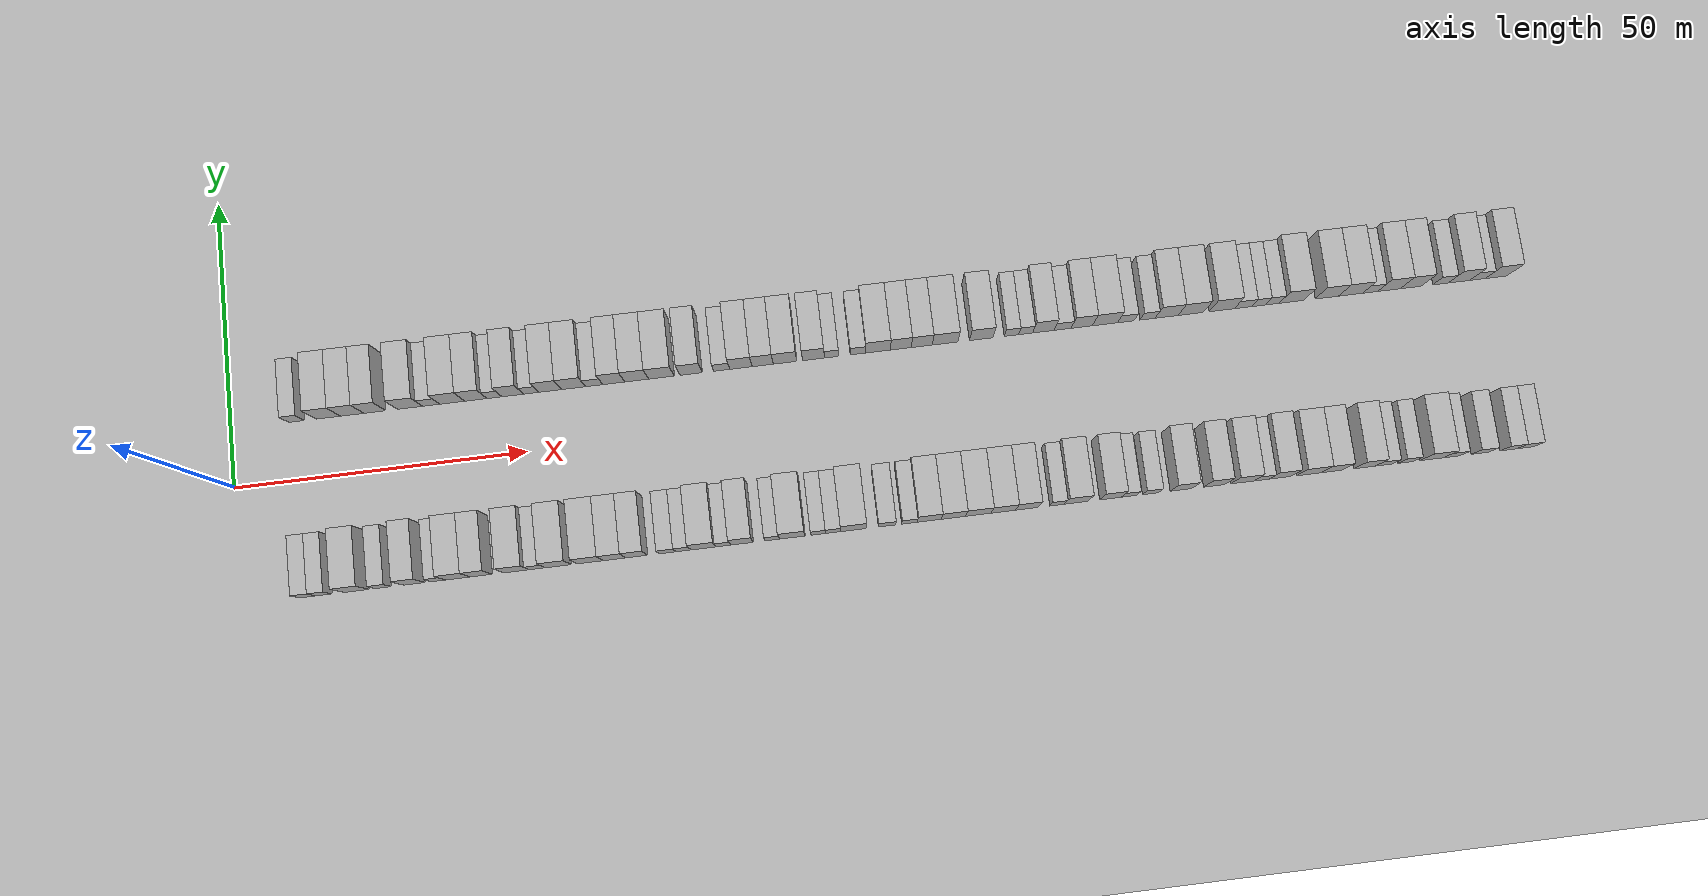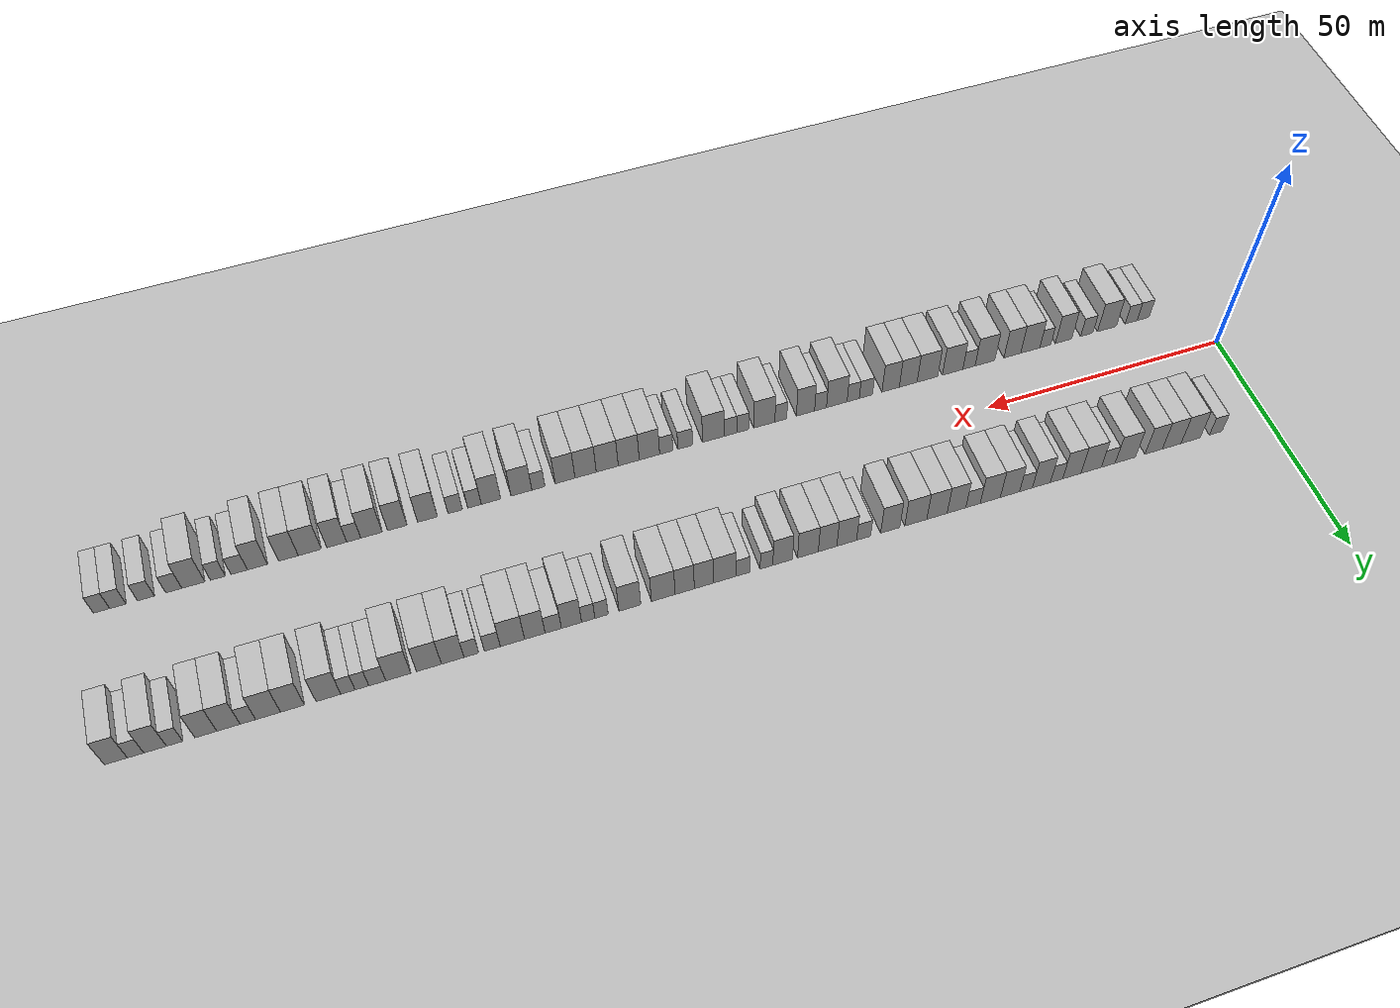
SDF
<?xml version="1.0" encoding="utf-8"?>

<sdf version="1.6">

   <world name="default">

      <gui fullscreen="0">

         <camera name="user_camera">

            <pose>-15 0 4.57585 0 0 0</pose>

            <view_controller>orbit</view_controller>

         </camera>

      </gui>

      <scene>

         <sky>

           <clouds>

             <speed>12</speed>

           </clouds>

         </sky>

         <ambient>0.4 0.4 0.4 1</ambient>

         <background>0.7 0.7 0.7 1</background>

         <shadows>1</shadows>

      </scene>

      <gravity>0 0 -9.8066</gravity>

      <magnetic_field>6e-06 2.3e-05 -4.2e-05</magnetic_field>

      <physics default="0" name="default_physics" type="ode">

         <ode>

            <solver>

               <type>quick</type>

               <iters>10</iters>

               <sor>1.0</sor>

               <use_dynamic_moi_rescaling>0</use_dynamic_moi_rescaling>

            </solver>

            <constraints>

               <cfm>0</cfm>

               <erp>0.2</erp>

               <contact_max_correcting_vel>100</contact_max_correcting_vel>

               <contact_surface_layer>0.001</contact_surface_layer>

            </constraints>

         </ode>

         <max_step_size>0.004</max_step_size>

         <real_time_factor>1</real_time_factor>

         <real_time_update_rate>250</real_time_update_rate>

      </physics>

      <light name="sun" type="directional">

         <cast_shadows>1</cast_shadows>

         <pose>0 0 10 0 0 0</pose>

         <diffuse>0.8 0.8 0.8 1</diffuse>

         <specular>0.2 0.2 0.2 1</specular>

         <attenuation>

            <range>1000</range>

            <constant>0.9</constant>

            <linear>0.01</linear>

            <quadratic>0.001</quadratic>

         </attenuation>

         <direction>-0.5 0.1 -0.9</direction>

      </light>

      <include>

         <name>ground_plane_1</name>

         <uri>model://HANNAS_ground_plane</uri>

         <pose>0 0 0  0 0 0</pose>

      </include>

      <include>

         <name>ground_plane_2</name>

         <uri>model://HANNAS_ground_plane</uri>

         <pose>100 0 0  0 0 0</pose>

      </include>

      <model name="building_1">

         <static>1</static>

         <pose frame="">11.3692 15.0000 0 0.000000 0.000000 1.570796</pose>

         <link name="link">

            <pose frame="">0 0 3.00 0 0 0</pose>

            <collision name="collision">

               <geometry>

                  <box>

                     <size>10.0000 2.7384 6.0000</size>

                  </box>

               </geometry>

               <max_contacts>10</max_contacts>

               <surface>

                  <contact>

                     <ode/>

                  </contact>

                  <bounce/>

                  <friction>

                     <torsional>

                        <ode/>

                     </torsional>

                     <ode/>

                  </friction>

               </surface>

            </collision>

            <visual name="visual">

               <cast_shadows>0</cast_shadows>

               <geometry>

                  <box>

                     <size>10.0000 2.7384 6.0000</size>

                  </box>

               </geometry>

               <material>

                  <script>

                     <uri>model://HANNAS_wall/materials/scripts</uri>

                     <uri>model://HANNAS_wall/materials/textures</uri>

                     <name>vrc/HANNAS_wall</name>

                  </script>

               </material>

            </visual>

            <self_collide>0</self_collide>

            <enable_wind>0</enable_wind>

            <kinematic>0</kinematic>

         </link>

      </model>

      <model name="building_2">

         <static>1</static>

         <pose frame="">16.8051 15.0000 0 0.000000 0.000000 1.570796</pose>

         <link name="link">

            <pose frame="">0 0 4.50 0 0 0</pose>

            <collision name="collision">

               <geometry>

                  <box>

                     <size>10.0000 4.1334 9.0000</size>

                  </box>

               </geometry>

               <max_contacts>10</max_contacts>

               <surface>

                  <contact>

                     <ode/>

                  </contact>

                  <bounce/>

                  <friction>

                     <torsional>

                        <ode/>

                     </torsional>

                     <ode/>

                  </friction>

               </surface>

            </collision>

            <visual name="visual">

               <cast_shadows>0</cast_shadows>

               <geometry>

                  <box>

                     <size>10.0000 4.1334 9.0000</size>

                  </box>

               </geometry>

               <material>

                  <script>

                     <uri>model://HANNAS_wall/materials/scripts</uri>

                     <uri>model://HANNAS_wall/materials/textures</uri>

                     <name>vrc/HANNAS_wall</name>

                  </script>

               </material>

            </visual>

            <self_collide>0</self_collide>

            <enable_wind>0</enable_wind>

            <kinematic>0</kinematic>

         </link>

      </model>

      <model name="building_3">

         <static>1</static>

         <pose frame="">20.8733 15.0000 0 0.000000 0.000000 1.570796</pose>

         <link name="link">

            <pose frame="">0 0 4.50 0 0 0</pose>

            <collision name="collision">

               <geometry>

                  <box>

                     <size>10.0000 4.0029 9.0000</size>

                  </box>

               </geometry>

               <max_contacts>10</max_contacts>

               <surface>

                  <contact>

                     <ode/>

                  </contact>

                  <bounce/>

                  <friction>

                     <torsional>

                        <ode/>

                     </torsional>

                     <ode/>

                  </friction>

               </surface>

            </collision>

            <visual name="visual">

               <cast_shadows>0</cast_shadows>

               <geometry>

                  <box>

                     <size>10.0000 4.0029 9.0000</size>

                  </box>

               </geometry>

               <material>

                  <script>

                     <uri>model://HANNAS_wall/materials/scripts</uri>

                     <uri>model://HANNAS_wall/materials/textures</uri>

                     <name>vrc/HANNAS_wall</name>

                  </script>

               </material>

            </visual>

            <self_collide>0</self_collide>

            <enable_wind>0</enable_wind>

            <kinematic>0</kinematic>

         </link>

      </model>

      <model name="building_4">

         <static>1</static>

         <pose frame="">24.7356 15.0000 0 0.000000 0.000000 1.570796</pose>

         <link name="link">

            <pose frame="">0 0 4.50 0 0 0</pose>

            <collision name="collision">

               <geometry>

                  <box>

                     <size>10.0000 3.7217 9.0000</size>

                  </box>

               </geometry>

               <max_contacts>10</max_contacts>

               <surface>

                  <contact>

                     <ode/>

                  </contact>

                  <bounce/>

                  <friction>

                     <torsional>

                        <ode/>

                     </torsional>

                     <ode/>

                  </friction>

               </surface>

            </collision>

            <visual name="visual">

               <cast_shadows>0</cast_shadows>

               <geometry>

                  <box>

                     <size>10.0000 3.7217 9.0000</size>

                  </box>

               </geometry>

               <material>

                  <script>

                     <uri>model://HANNAS_wall/materials/scripts</uri>

                     <uri>model://HANNAS_wall/materials/textures</uri>

                     <name>vrc/HANNAS_wall</name>

                  </script>

               </material>

            </visual>

            <self_collide>0</self_collide>

            <enable_wind>0</enable_wind>

            <kinematic>0</kinematic>

         </link>

      </model>

      <model name="building_5">

         <static>1</static>

         <pose frame="">30.7625 15.0000 0 0.000000 0.000000 1.570796</pose>

         <link name="link">

            <pose frame="">0 0 4.50 0 0 0</pose>

            <collision name="collision">

               <geometry>

                  <box>

                     <size>10.0000 4.3320 9.0000</size>

                  </box>

               </geometry>

               <max_contacts>10</max_contacts>

               <surface>

                  <contact>

                     <ode/>

                  </contact>

                  <bounce/>

                  <friction>

                     <torsional>

                        <ode/>

                     </torsional>

                     <ode/>

                  </friction>

               </surface>

            </collision>

            <visual name="visual">

               <cast_shadows>0</cast_shadows>

               <geometry>

                  <box>

                     <size>10.0000 4.3320 9.0000</size>

                  </box>

               </geometry>

               <material>

                  <script>

                     <uri>model://HANNAS_wall/materials/scripts</uri>

                     <uri>model://HANNAS_wall/materials/textures</uri>

                     <name>vrc/HANNAS_wall</name>

                  </script>

               </material>

            </visual>

            <self_collide>0</self_collide>

            <enable_wind>0</enable_wind>

            <kinematic>0</kinematic>

         </link>

      </model>

      <model name="building_6">

         <static>1</static>

         <pose frame="">34.3926 15.0000 0 0.000000 0.000000 1.570796</pose>

         <link name="link">

            <pose frame="">0 0 3.00 0 0 0</pose>

            <collision name="collision">

               <geometry>

                  <box>

                     <size>10.0000 2.9282 6.0000</size>

                  </box>

               </geometry>

               <max_contacts>10</max_contacts>

               <surface>

                  <contact>

                     <ode/>

                  </contact>

                  <bounce/>

                  <friction>

                     <torsional>

                        <ode/>

                     </torsional>

                     <ode/>

                  </friction>

               </surface>

            </collision>

            <visual name="visual">

               <cast_shadows>0</cast_shadows>

               <geometry>

                  <box>

                     <size>10.0000 2.9282 6.0000</size>

                  </box>

               </geometry>

               <material>

                  <script>

                     <uri>model://HANNAS_wall/materials/scripts</uri>

                     <uri>model://HANNAS_wall/materials/textures</uri>

                     <name>vrc/HANNAS_wall</name>

                  </script>

               </material>

            </visual>

            <self_collide>0</self_collide>

            <enable_wind>0</enable_wind>

            <kinematic>0</kinematic>

         </link>

      </model>

      <model name="building_7">

         <static>1</static>

         <pose frame="">37.9927 15.0000 0 0.000000 0.000000 1.570796</pose>

         <link name="link">

            <pose frame="">0 0 4.50 0 0 0</pose>

            <collision name="collision">

               <geometry>

                  <box>

                     <size>10.0000 4.2720 9.0000</size>

                  </box>

               </geometry>

               <max_contacts>10</max_contacts>

               <surface>

                  <contact>

                     <ode/>

                  </contact>

                  <bounce/>

                  <friction>

                     <torsional>

                        <ode/>

                     </torsional>

                     <ode/>

                  </friction>

               </surface>

            </collision>

            <visual name="visual">

               <cast_shadows>0</cast_shadows>

               <geometry>

                  <box>

                     <size>10.0000 4.2720 9.0000</size>

                  </box>

               </geometry>

               <material>

                  <script>

                     <uri>model://HANNAS_wall/materials/scripts</uri>

                     <uri>model://HANNAS_wall/materials/textures</uri>

                     <name>vrc/HANNAS_wall</name>

                  </script>

               </material>

            </visual>

            <self_collide>0</self_collide>

            <enable_wind>0</enable_wind>

            <kinematic>0</kinematic>

         </link>

      </model>

      <model name="building_8">

         <static>1</static>

         <pose frame="">42.0451 15.0000 0 0.000000 0.000000 1.570796</pose>

         <link name="link">

            <pose frame="">0 0 4.50 0 0 0</pose>

            <collision name="collision">

               <geometry>

                  <box>

                     <size>10.0000 3.8328 9.0000</size>

                  </box>

               </geometry>

               <max_contacts>10</max_contacts>

               <surface>

                  <contact>

                     <ode/>

                  </contact>

                  <bounce/>

                  <friction>

                     <torsional>

                        <ode/>

                     </torsional>

                     <ode/>

                  </friction>

               </surface>

            </collision>

            <visual name="visual">

               <cast_shadows>0</cast_shadows>

               <geometry>

                  <box>

                     <size>10.0000 3.8328 9.0000</size>

                  </box>

               </geometry>

               <material>

                  <script>

                     <uri>model://HANNAS_wall/materials/scripts</uri>

                     <uri>model://HANNAS_wall/materials/textures</uri>

                     <name>vrc/HANNAS_wall</name>

                  </script>

               </material>

            </visual>

            <self_collide>0</self_collide>

            <enable_wind>0</enable_wind>

            <kinematic>0</kinematic>

         </link>

      </model>

      <model name="building_9">

         <static>1</static>

         <pose frame="">45.2384 15.0000 0 0.000000 0.000000 1.570796</pose>

         <link name="link">

            <pose frame="">0 0 3.00 0 0 0</pose>

            <collision name="collision">

               <geometry>

                  <box>

                     <size>10.0000 2.5539 6.0000</size>

                  </box>

               </geometry>

               <max_contacts>10</max_contacts>

               <surface>

                  <contact>

                     <ode/>

                  </contact>

                  <bounce/>

                  <friction>

                     <torsional>

                        <ode/>

                     </torsional>

                     <ode/>

                  </friction>

               </surface>

            </collision>

            <visual name="visual">

               <cast_shadows>0</cast_shadows>

               <geometry>

                  <box>

                     <size>10.0000 2.5539 6.0000</size>

                  </box>

               </geometry>

               <material>

                  <script>

                     <uri>model://HANNAS_wall/materials/scripts</uri>

                     <uri>model://HANNAS_wall/materials/textures</uri>

                     <name>vrc/HANNAS_wall</name>

                  </script>

               </material>

            </visual>

            <self_collide>0</self_collide>

            <enable_wind>0</enable_wind>

            <kinematic>0</kinematic>

         </link>

      </model>

      <model name="building_10">

         <static>1</static>

         <pose frame="">48.3754 15.0000 0 0.000000 0.000000 1.570796</pose>

         <link name="link">

            <pose frame="">0 0 4.50 0 0 0</pose>

            <collision name="collision">

               <geometry>

                  <box>

                     <size>10.0000 3.7200 9.0000</size>

                  </box>

               </geometry>

               <max_contacts>10</max_contacts>

               <surface>

                  <contact>

                     <ode/>

                  </contact>

                  <bounce/>

                  <friction>

                     <torsional>

                        <ode/>

                     </torsional>

                     <ode/>

                  </friction>

               </surface>

            </collision>

            <visual name="visual">

               <cast_shadows>0</cast_shadows>

               <geometry>

                  <box>

                     <size>10.0000 3.7200 9.0000</size>

                  </box>

               </geometry>

               <material>

                  <script>

                     <uri>model://HANNAS_wall/materials/scripts</uri>

                     <uri>model://HANNAS_wall/materials/textures</uri>

                     <name>vrc/HANNAS_wall</name>

                  </script>

               </material>

            </visual>

            <self_collide>0</self_collide>

            <enable_wind>0</enable_wind>

            <kinematic>0</kinematic>

         </link>

      </model>

      <model name="building_11">

         <static>1</static>

         <pose frame="">51.5613 15.0000 0 0.000000 0.000000 1.570796</pose>

         <link name="link">

            <pose frame="">0 0 3.00 0 0 0</pose>

            <collision name="collision">

               <geometry>

                  <box>

                     <size>10.0000 2.6518 6.0000</size>

                  </box>

               </geometry>

               <max_contacts>10</max_contacts>

               <surface>

                  <contact>

                     <ode/>

                  </contact>

                  <bounce/>

                  <friction>

                     <torsional>

                        <ode/>

                     </torsional>

                     <ode/>

                  </friction>

               </surface>

            </collision>

            <visual name="visual">

               <cast_shadows>0</cast_shadows>

               <geometry>

                  <box>

                     <size>10.0000 2.6518 6.0000</size>

                  </box>

               </geometry>

               <material>

                  <script>

                     <uri>model://HANNAS_wall/materials/scripts</uri>

                     <uri>model://HANNAS_wall/materials/textures</uri>

                     <name>vrc/HANNAS_wall</name>

                  </script>

               </material>

            </visual>

            <self_collide>0</self_collide>

            <enable_wind>0</enable_wind>

            <kinematic>0</kinematic>

         </link>

      </model>

      <model name="building_12">

         <static>1</static>

         <pose frame="">54.8684 15.0000 0 0.000000 0.000000 1.570796</pose>

         <link name="link">

            <pose frame="">0 0 4.50 0 0 0</pose>

            <collision name="collision">

               <geometry>

                  <box>

                     <size>10.0000 3.9625 9.0000</size>

                  </box>

               </geometry>

               <max_contacts>10</max_contacts>

               <surface>

                  <contact>

                     <ode/>

                  </contact>

                  <bounce/>

                  <friction>

                     <torsional>

                        <ode/>

                     </torsional>

                     <ode/>

                  </friction>

               </surface>

            </collision>

            <visual name="visual">

               <cast_shadows>0</cast_shadows>

               <geometry>

                  <box>

                     <size>10.0000 3.9625 9.0000</size>

                  </box>

               </geometry>

               <material>

                  <script>

                     <uri>model://HANNAS_wall/materials/scripts</uri>

                     <uri>model://HANNAS_wall/materials/textures</uri>

                     <name>vrc/HANNAS_wall</name>

                  </script>

               </material>

            </visual>

            <self_collide>0</self_collide>

            <enable_wind>0</enable_wind>

            <kinematic>0</kinematic>

         </link>

      </model>

      <model name="building_13">

         <static>1</static>

         <pose frame="">58.9045 15.0000 0 0.000000 0.000000 1.570796</pose>

         <link name="link">

            <pose frame="">0 0 4.50 0 0 0</pose>

            <collision name="collision">

               <geometry>

                  <box>

                     <size>10.0000 4.1097 9.0000</size>

                  </box>

               </geometry>

               <max_contacts>10</max_contacts>

               <surface>

                  <contact>

                     <ode/>

                  </contact>

                  <bounce/>

                  <friction>

                     <torsional>

                        <ode/>

                     </torsional>

                     <ode/>

                  </friction>

               </surface>

            </collision>

            <visual name="visual">

               <cast_shadows>0</cast_shadows>

               <geometry>

                  <box>

                     <size>10.0000 4.1097 9.0000</size>

                  </box>

               </geometry>

               <material>

                  <script>

                     <uri>model://HANNAS_wall/materials/scripts</uri>

                     <uri>model://HANNAS_wall/materials/textures</uri>

                     <name>vrc/HANNAS_wall</name>

                  </script>

               </material>

            </visual>

            <self_collide>0</self_collide>

            <enable_wind>0</enable_wind>

            <kinematic>0</kinematic>

         </link>

      </model>

      <model name="building_14">

         <static>1</static>

         <pose frame="">62.4323 15.0000 0 0.000000 0.000000 1.570796</pose>

         <link name="link">

            <pose frame="">0 0 3.00 0 0 0</pose>

            <collision name="collision">

               <geometry>

                  <box>

                     <size>10.0000 2.9458 6.0000</size>

                  </box>

               </geometry>

               <max_contacts>10</max_contacts>

               <surface>

                  <contact>

                     <ode/>

                  </contact>

                  <bounce/>

                  <friction>

                     <torsional>

                        <ode/>

                     </torsional>

                     <ode/>

                  </friction>

               </surface>

            </collision>

            <visual name="visual">

               <cast_shadows>0</cast_shadows>

               <geometry>

                  <box>

                     <size>10.0000 2.9458 6.0000</size>

                  </box>

               </geometry>

               <material>

                  <script>

                     <uri>model://HANNAS_wall/materials/scripts</uri>

                     <uri>model://HANNAS_wall/materials/textures</uri>

                     <name>vrc/HANNAS_wall</name>

                  </script>

               </material>

            </visual>

            <self_collide>0</self_collide>

            <enable_wind>0</enable_wind>

            <kinematic>0</kinematic>

         </link>

      </model>

      <model name="building_15">

         <static>1</static>

         <pose frame="">65.8019 15.0000 0 0.000000 0.000000 1.570796</pose>

         <link name="link">

            <pose frame="">0 0 4.50 0 0 0</pose>

            <collision name="collision">

               <geometry>

                  <box>

                     <size>10.0000 3.7934 9.0000</size>

                  </box>

               </geometry>

               <max_contacts>10</max_contacts>

               <surface>

                  <contact>

                     <ode/>

                  </contact>

                  <bounce/>

                  <friction>

                     <torsional>

                        <ode/>

                     </torsional>

                     <ode/>

                  </friction>

               </surface>

            </collision>

            <visual name="visual">

               <cast_shadows>0</cast_shadows>

               <geometry>

                  <box>

                     <size>10.0000 3.7934 9.0000</size>

                  </box>

               </geometry>

               <material>

                  <script>

                     <uri>model://HANNAS_wall/materials/scripts</uri>

                     <uri>model://HANNAS_wall/materials/textures</uri>

                     <name>vrc/HANNAS_wall</name>

                  </script>

               </material>

            </visual>

            <self_collide>0</self_collide>

            <enable_wind>0</enable_wind>

            <kinematic>0</kinematic>

         </link>

      </model>

      <model name="building_16">

         <static>1</static>

         <pose frame="">69.7563 15.0000 0 0.000000 0.000000 1.570796</pose>

         <link name="link">

            <pose frame="">0 0 4.50 0 0 0</pose>

            <collision name="collision">

               <geometry>

                  <box>

                     <size>10.0000 4.1156 9.0000</size>

                  </box>

               </geometry>

               <max_contacts>10</max_contacts>

               <surface>

                  <contact>

                     <ode/>

                  </contact>

                  <bounce/>

                  <friction>

                     <torsional>

                        <ode/>

                     </torsional>

                     <ode/>

                  </friction>

               </surface>

            </collision>

            <visual name="visual">

               <cast_shadows>0</cast_shadows>

               <geometry>

                  <box>

                     <size>10.0000 4.1156 9.0000</size>

                  </box>

               </geometry>

               <material>

                  <script>

                     <uri>model://HANNAS_wall/materials/scripts</uri>

                     <uri>model://HANNAS_wall/materials/textures</uri>

                     <name>vrc/HANNAS_wall</name>

                  </script>

               </material>

            </visual>

            <self_collide>0</self_collide>

            <enable_wind>0</enable_wind>

            <kinematic>0</kinematic>

         </link>

      </model>

      <model name="building_17">

         <static>1</static>

         <pose frame="">74.0166 15.0000 0 0.000000 0.000000 1.570796</pose>

         <link name="link">

            <pose frame="">0 0 4.50 0 0 0</pose>

            <collision name="collision">

               <geometry>

                  <box>

                     <size>10.0000 4.4050 9.0000</size>

                  </box>

               </geometry>

               <max_contacts>10</max_contacts>

               <surface>

                  <contact>

                     <ode/>

                  </contact>

                  <bounce/>

                  <friction>

                     <torsional>

                        <ode/>

                     </torsional>

                     <ode/>

                  </friction>

               </surface>

            </collision>

            <visual name="visual">

               <cast_shadows>0</cast_shadows>

               <geometry>

                  <box>

                     <size>10.0000 4.4050 9.0000</size>

                  </box>

               </geometry>

               <material>

                  <script>

                     <uri>model://HANNAS_wall/materials/scripts</uri>

                     <uri>model://HANNAS_wall/materials/textures</uri>

                     <name>vrc/HANNAS_wall</name>

                  </script>

               </material>

            </visual>

            <self_collide>0</self_collide>

            <enable_wind>0</enable_wind>

            <kinematic>0</kinematic>

         </link>

      </model>

      <model name="building_18">

         <static>1</static>

         <pose frame="">79.1240 15.0000 0 0.000000 0.000000 1.570796</pose>

         <link name="link">

            <pose frame="">0 0 4.50 0 0 0</pose>

            <collision name="collision">

               <geometry>

                  <box>

                     <size>10.0000 3.8099 9.0000</size>

                  </box>

               </geometry>

               <max_contacts>10</max_contacts>

               <surface>

                  <contact>

                     <ode/>

                  </contact>

                  <bounce/>

                  <friction>

                     <torsional>

                        <ode/>

                     </torsional>

                     <ode/>

                  </friction>

               </surface>

            </collision>

            <visual name="visual">

               <cast_shadows>0</cast_shadows>

               <geometry>

                  <box>

                     <size>10.0000 3.8099 9.0000</size>

                  </box>

               </geometry>

               <material>

                  <script>

                     <uri>model://HANNAS_wall/materials/scripts</uri>

                     <uri>model://HANNAS_wall/materials/textures</uri>

                     <name>vrc/HANNAS_wall</name>

                  </script>

               </material>

            </visual>

            <self_collide>0</self_collide>

            <enable_wind>0</enable_wind>

            <kinematic>0</kinematic>

         </link>

      </model>

      <model name="building_19">

         <static>1</static>

         <pose frame="">84.4165 15.0000 0 0.000000 0.000000 1.570796</pose>

         <link name="link">

            <pose frame="">0 0 3.00 0 0 0</pose>

            <collision name="collision">

               <geometry>

                  <box>

                     <size>10.0000 2.7750 6.0000</size>

                  </box>

               </geometry>

               <max_contacts>10</max_contacts>

               <surface>

                  <contact>

                     <ode/>

                  </contact>

                  <bounce/>

                  <friction>

                     <torsional>

                        <ode/>

                     </torsional>

                     <ode/>

                  </friction>

               </surface>

            </collision>

            <visual name="visual">

               <cast_shadows>0</cast_shadows>

               <geometry>

                  <box>

                     <size>10.0000 2.7750 6.0000</size>

                  </box>

               </geometry>

               <material>

                  <script>

                     <uri>model://HANNAS_wall/materials/scripts</uri>

                     <uri>model://HANNAS_wall/materials/textures</uri>

                     <name>vrc/HANNAS_wall</name>

                  </script>

               </material>

            </visual>

            <self_collide>0</self_collide>

            <enable_wind>0</enable_wind>

            <kinematic>0</kinematic>

         </link>

      </model>

      <model name="building_20">

         <static>1</static>

         <pose frame="">87.7496 15.0000 0 0.000000 0.000000 1.570796</pose>

         <link name="link">

            <pose frame="">0 0 4.50 0 0 0</pose>

            <collision name="collision">

               <geometry>

                  <box>

                     <size>10.0000 3.8914 9.0000</size>

                  </box>

               </geometry>

               <max_contacts>10</max_contacts>

               <surface>

                  <contact>

                     <ode/>

                  </contact>

                  <bounce/>

                  <friction>

                     <torsional>

                        <ode/>

                     </torsional>

                     <ode/>

                  </friction>

               </surface>

            </collision>

            <visual name="visual">

               <cast_shadows>0</cast_shadows>

               <geometry>

                  <box>

                     <size>10.0000 3.8914 9.0000</size>

                  </box>

               </geometry>

               <material>

                  <script>

                     <uri>model://HANNAS_wall/materials/scripts</uri>

                     <uri>model://HANNAS_wall/materials/textures</uri>

                     <name>vrc/HANNAS_wall</name>

                  </script>

               </material>

            </visual>

            <self_collide>0</self_collide>

            <enable_wind>0</enable_wind>

            <kinematic>0</kinematic>

         </link>

      </model>

      <model name="building_21">

         <static>1</static>

         <pose frame="">91.5132 15.0000 0 0.000000 0.000000 1.570796</pose>

         <link name="link">

            <pose frame="">0 0 4.50 0 0 0</pose>

            <collision name="collision">

               <geometry>

                  <box>

                     <size>10.0000 3.6357 9.0000</size>

                  </box>

               </geometry>

               <max_contacts>10</max_contacts>

               <surface>

                  <contact>

                     <ode/>

                  </contact>

                  <bounce/>

                  <friction>

                     <torsional>

                        <ode/>

                     </torsional>

                     <ode/>

                  </friction>

               </surface>

            </collision>

            <visual name="visual">

               <cast_shadows>0</cast_shadows>

               <geometry>

                  <box>

                     <size>10.0000 3.6357 9.0000</size>

                  </box>

               </geometry>

               <material>

                  <script>

                     <uri>model://HANNAS_wall/materials/scripts</uri>

                     <uri>model://HANNAS_wall/materials/textures</uri>

                     <name>vrc/HANNAS_wall</name>

                  </script>

               </material>

            </visual>

            <self_collide>0</self_collide>

            <enable_wind>0</enable_wind>

            <kinematic>0</kinematic>

         </link>

      </model>

      <model name="building_22">

         <static>1</static>

         <pose frame="">95.3576 15.0000 0 0.000000 0.000000 1.570796</pose>

         <link name="link">

            <pose frame="">0 0 4.50 0 0 0</pose>

            <collision name="collision">

               <geometry>

                  <box>

                     <size>10.0000 4.0532 9.0000</size>

                  </box>

               </geometry>

               <max_contacts>10</max_contacts>

               <surface>

                  <contact>

                     <ode/>

                  </contact>

                  <bounce/>

                  <friction>

                     <torsional>

                        <ode/>

                     </torsional>

                     <ode/>

                  </friction>

               </surface>

            </collision>

            <visual name="visual">

               <cast_shadows>0</cast_shadows>

               <geometry>

                  <box>

                     <size>10.0000 4.0532 9.0000</size>

                  </box>

               </geometry>

               <material>

                  <script>

                     <uri>model://HANNAS_wall/materials/scripts</uri>

                     <uri>model://HANNAS_wall/materials/textures</uri>

                     <name>vrc/HANNAS_wall</name>

                  </script>

               </material>

            </visual>

            <self_collide>0</self_collide>

            <enable_wind>0</enable_wind>

            <kinematic>0</kinematic>

         </link>

      </model>

      <model name="building_23">

         <static>1</static>

         <pose frame="">100.2773 15.0000 0 0.000000 0.000000 1.570796</pose>

         <link name="link">

            <pose frame="">0 0 4.50 0 0 0</pose>

            <collision name="collision">

               <geometry>

                  <box>

                     <size>10.0000 3.7861 9.0000</size>

                  </box>

               </geometry>

               <max_contacts>10</max_contacts>

               <surface>

                  <contact>

                     <ode/>

                  </contact>

                  <bounce/>

                  <friction>

                     <torsional>

                        <ode/>

                     </torsional>

                     <ode/>

                  </friction>

               </surface>

            </collision>

            <visual name="visual">

               <cast_shadows>0</cast_shadows>

               <geometry>

                  <box>

                     <size>10.0000 3.7861 9.0000</size>

                  </box>

               </geometry>

               <material>

                  <script>

                     <uri>model://HANNAS_wall/materials/scripts</uri>

                     <uri>model://HANNAS_wall/materials/textures</uri>

                     <name>vrc/HANNAS_wall</name>

                  </script>

               </material>

            </visual>

            <self_collide>0</self_collide>

            <enable_wind>0</enable_wind>

            <kinematic>0</kinematic>

         </link>

      </model>

      <model name="building_24">

         <static>1</static>

         <pose frame="">103.3981 15.0000 0 0.000000 0.000000 1.570796</pose>

         <link name="link">

            <pose frame="">0 0 3.00 0 0 0</pose>

            <collision name="collision">

               <geometry>

                  <box>

                     <size>10.0000 2.4554 6.0000</size>

                  </box>

               </geometry>

               <max_contacts>10</max_contacts>

               <surface>

                  <contact>

                     <ode/>

                  </contact>

                  <bounce/>

                  <friction>

                     <torsional>

                        <ode/>

                     </torsional>

                     <ode/>

                  </friction>

               </surface>

            </collision>

            <visual name="visual">

               <cast_shadows>0</cast_shadows>

               <geometry>

                  <box>

                     <size>10.0000 2.4554 6.0000</size>

                  </box>

               </geometry>

               <material>

                  <script>

                     <uri>model://HANNAS_wall/materials/scripts</uri>

                     <uri>model://HANNAS_wall/materials/textures</uri>

                     <name>vrc/HANNAS_wall</name>

                  </script>

               </material>

            </visual>

            <self_collide>0</self_collide>

            <enable_wind>0</enable_wind>

            <kinematic>0</kinematic>

         </link>

      </model>

      <model name="building_25">

         <static>1</static>

         <pose frame="">107.9604 15.0000 0 0.000000 0.000000 1.570796</pose>

         <link name="link">

            <pose frame="">0 0 3.00 0 0 0</pose>

            <collision name="collision">

               <geometry>

                  <box>

                     <size>10.0000 2.6691 6.0000</size>

                  </box>

               </geometry>

               <max_contacts>10</max_contacts>

               <surface>

                  <contact>

                     <ode/>

                  </contact>

                  <bounce/>

                  <friction>

                     <torsional>

                        <ode/>

                     </torsional>

                     <ode/>

                  </friction>

               </surface>

            </collision>

            <visual name="visual">

               <cast_shadows>0</cast_shadows>

               <geometry>

                  <box>

                     <size>10.0000 2.6691 6.0000</size>

                  </box>

               </geometry>

               <material>

                  <script>

                     <uri>model://HANNAS_wall/materials/scripts</uri>

                     <uri>model://HANNAS_wall/materials/textures</uri>

                     <name>vrc/HANNAS_wall</name>

                  </script>

               </material>

            </visual>

            <self_collide>0</self_collide>

            <enable_wind>0</enable_wind>

            <kinematic>0</kinematic>

         </link>

      </model>

      <model name="building_26">

         <static>1</static>

         <pose frame="">111.4401 15.0000 0 0.000000 0.000000 1.570796</pose>

         <link name="link">

            <pose frame="">0 0 4.50 0 0 0</pose>

            <collision name="collision">

               <geometry>

                  <box>

                     <size>10.0000 4.2903 9.0000</size>

                  </box>

               </geometry>

               <max_contacts>10</max_contacts>

               <surface>

                  <contact>

                     <ode/>

                  </contact>

                  <bounce/>

                  <friction>

                     <torsional>

                        <ode/>

                     </torsional>

                     <ode/>

                  </friction>

               </surface>

            </collision>

            <visual name="visual">

               <cast_shadows>0</cast_shadows>

               <geometry>

                  <box>

                     <size>10.0000 4.2903 9.0000</size>

                  </box>

               </geometry>

               <material>

                  <script>

                     <uri>model://HANNAS_wall/materials/scripts</uri>

                     <uri>model://HANNAS_wall/materials/textures</uri>

                     <name>vrc/HANNAS_wall</name>

                  </script>

               </material>

            </visual>

            <self_collide>0</self_collide>

            <enable_wind>0</enable_wind>

            <kinematic>0</kinematic>

         </link>

      </model>

      <model name="building_27">

         <static>1</static>

         <pose frame="">115.3962 15.0000 0 0.000000 0.000000 1.570796</pose>

         <link name="link">

            <pose frame="">0 0 4.50 0 0 0</pose>

            <collision name="collision">

               <geometry>

                  <box>

                     <size>10.0000 3.6218 9.0000</size>

                  </box>

               </geometry>

               <max_contacts>10</max_contacts>

               <surface>

                  <contact>

                     <ode/>

                  </contact>

                  <bounce/>

                  <friction>

                     <torsional>

                        <ode/>

                     </torsional>

                     <ode/>

                  </friction>

               </surface>

            </collision>

            <visual name="visual">

               <cast_shadows>0</cast_shadows>

               <geometry>

                  <box>

                     <size>10.0000 3.6218 9.0000</size>

                  </box>

               </geometry>

               <material>

                  <script>

                     <uri>model://HANNAS_wall/materials/scripts</uri>

                     <uri>model://HANNAS_wall/materials/textures</uri>

                     <name>vrc/HANNAS_wall</name>

                  </script>

               </material>

            </visual>

            <self_collide>0</self_collide>

            <enable_wind>0</enable_wind>

            <kinematic>0</kinematic>

         </link>

      </model>

      <model name="building_28">

         <static>1</static>

         <pose frame="">119.0243 15.0000 0 0.000000 0.000000 1.570796</pose>

         <link name="link">

            <pose frame="">0 0 4.50 0 0 0</pose>

            <collision name="collision">

               <geometry>

                  <box>

                     <size>10.0000 3.6346 9.0000</size>

                  </box>

               </geometry>

               <max_contacts>10</max_contacts>

               <surface>

                  <contact>

                     <ode/>

                  </contact>

                  <bounce/>

                  <friction>

                     <torsional>

                        <ode/>

                     </torsional>

                     <ode/>

                  </friction>

               </surface>

            </collision>

            <visual name="visual">

               <cast_shadows>0</cast_shadows>

               <geometry>

                  <box>

                     <size>10.0000 3.6346 9.0000</size>

                  </box>

               </geometry>

               <material>

                  <script>

                     <uri>model://HANNAS_wall/materials/scripts</uri>

                     <uri>model://HANNAS_wall/materials/textures</uri>

                     <name>vrc/HANNAS_wall</name>

                  </script>

               </material>

            </visual>

            <self_collide>0</self_collide>

            <enable_wind>0</enable_wind>

            <kinematic>0</kinematic>

         </link>

      </model>

      <model name="building_29">

         <static>1</static>

         <pose frame="">123.0679 15.0000 0 0.000000 0.000000 1.570796</pose>

         <link name="link">

            <pose frame="">0 0 4.50 0 0 0</pose>

            <collision name="collision">

               <geometry>

                  <box>

                     <size>10.0000 4.4526 9.0000</size>

                  </box>

               </geometry>

               <max_contacts>10</max_contacts>

               <surface>

                  <contact>

                     <ode/>

                  </contact>

                  <bounce/>

                  <friction>

                     <torsional>

                        <ode/>

                     </torsional>

                     <ode/>

                  </friction>

               </surface>

            </collision>

            <visual name="visual">

               <cast_shadows>0</cast_shadows>

               <geometry>

                  <box>

                     <size>10.0000 4.4526 9.0000</size>

                  </box>

               </geometry>

               <material>

                  <script>

                     <uri>model://HANNAS_wall/materials/scripts</uri>

                     <uri>model://HANNAS_wall/materials/textures</uri>

                     <name>vrc/HANNAS_wall</name>

                  </script>

               </material>

            </visual>

            <self_collide>0</self_collide>

            <enable_wind>0</enable_wind>

            <kinematic>0</kinematic>

         </link>

      </model>

      <model name="building_30">

         <static>1</static>

         <pose frame="">129.3301 15.0000 0 0.000000 0.000000 1.570796</pose>

         <link name="link">

            <pose frame="">0 0 4.50 0 0 0</pose>

            <collision name="collision">

               <geometry>

                  <box>

                     <size>10.0000 4.0718 9.0000</size>

                  </box>

               </geometry>

               <max_contacts>10</max_contacts>

               <surface>

                  <contact>

                     <ode/>

                  </contact>

                  <bounce/>

                  <friction>

                     <torsional>

                        <ode/>

                     </torsional>

                     <ode/>

                  </friction>

               </surface>

            </collision>

            <visual name="visual">

               <cast_shadows>0</cast_shadows>

               <geometry>

                  <box>

                     <size>10.0000 4.0718 9.0000</size>

                  </box>

               </geometry>

               <material>

                  <script>

                     <uri>model://HANNAS_wall/materials/scripts</uri>

                     <uri>model://HANNAS_wall/materials/textures</uri>

                     <name>vrc/HANNAS_wall</name>

                  </script>

               </material>

            </visual>

            <self_collide>0</self_collide>

            <enable_wind>0</enable_wind>

            <kinematic>0</kinematic>

         </link>

      </model>

      <model name="building_31">

         <static>1</static>

         <pose frame="">134.6011 15.0000 0 0.000000 0.000000 1.570796</pose>

         <link name="link">

            <pose frame="">0 0 3.00 0 0 0</pose>

            <collision name="collision">

               <geometry>

                  <box>

                     <size>10.0000 2.4702 6.0000</size>

                  </box>

               </geometry>

               <max_contacts>10</max_contacts>

               <surface>

                  <contact>

                     <ode/>

                  </contact>

                  <bounce/>

                  <friction>

                     <torsional>

                        <ode/>

                     </torsional>

                     <ode/>

                  </friction>

               </surface>

            </collision>

            <visual name="visual">

               <cast_shadows>0</cast_shadows>

               <geometry>

                  <box>

                     <size>10.0000 2.4702 6.0000</size>

                  </box>

               </geometry>

               <material>

                  <script>

                     <uri>model://HANNAS_wall/materials/scripts</uri>

                     <uri>model://HANNAS_wall/materials/textures</uri>

                     <name>vrc/HANNAS_wall</name>

                  </script>

               </material>

            </visual>

            <self_collide>0</self_collide>

            <enable_wind>0</enable_wind>

            <kinematic>0</kinematic>

         </link>

      </model>

      <model name="building_32">

         <static>1</static>

         <pose frame="">137.0660 15.0000 0 0.000000 0.000000 1.570796</pose>

         <link name="link">

            <pose frame="">0 0 3.00 0 0 0</pose>

            <collision name="collision">

               <geometry>

                  <box>

                     <size>10.0000 2.4595 6.0000</size>

                  </box>

               </geometry>

               <max_contacts>10</max_contacts>

               <surface>

                  <contact>

                     <ode/>

                  </contact>

                  <bounce/>

                  <friction>

                     <torsional>

                        <ode/>

                     </torsional>

                     <ode/>

                  </friction>

               </surface>

            </collision>

            <visual name="visual">

               <cast_shadows>0</cast_shadows>

               <geometry>

                  <box>

                     <size>10.0000 2.4595 6.0000</size>

                  </box>

               </geometry>

               <material>

                  <script>

                     <uri>model://HANNAS_wall/materials/scripts</uri>

                     <uri>model://HANNAS_wall/materials/textures</uri>

                     <name>vrc/HANNAS_wall</name>

                  </script>

               </material>

            </visual>

            <self_collide>0</self_collide>

            <enable_wind>0</enable_wind>

            <kinematic>0</kinematic>

         </link>

      </model>

      <model name="building_33">

         <static>1</static>

         <pose frame="">140.1525 15.0000 0 0.000000 0.000000 1.570796</pose>

         <link name="link">

            <pose frame="">0 0 4.50 0 0 0</pose>

            <collision name="collision">

               <geometry>

                  <box>

                     <size>10.0000 3.7135 9.0000</size>

                  </box>

               </geometry>

               <max_contacts>10</max_contacts>

               <surface>

                  <contact>

                     <ode/>

                  </contact>

                  <bounce/>

                  <friction>

                     <torsional>

                        <ode/>

                     </torsional>

                     <ode/>

                  </friction>

               </surface>

            </collision>

            <visual name="visual">

               <cast_shadows>0</cast_shadows>

               <geometry>

                  <box>

                     <size>10.0000 3.7135 9.0000</size>

                  </box>

               </geometry>

               <material>

                  <script>

                     <uri>model://HANNAS_wall/materials/scripts</uri>

                     <uri>model://HANNAS_wall/materials/textures</uri>

                     <name>vrc/HANNAS_wall</name>

                  </script>

               </material>

            </visual>

            <self_collide>0</self_collide>

            <enable_wind>0</enable_wind>

            <kinematic>0</kinematic>

         </link>

      </model>

      <model name="building_34">

         <static>1</static>

         <pose frame="">143.5038 15.0000 0 0.000000 0.000000 1.570796</pose>

         <link name="link">

            <pose frame="">0 0 3.00 0 0 0</pose>

            <collision name="collision">

               <geometry>

                  <box>

                     <size>10.0000 2.9892 6.0000</size>

                  </box>

               </geometry>

               <max_contacts>10</max_contacts>

               <surface>

                  <contact>

                     <ode/>

                  </contact>

                  <bounce/>

                  <friction>

                     <torsional>

                        <ode/>

                     </torsional>

                     <ode/>

                  </friction>

               </surface>

            </collision>

            <visual name="visual">

               <cast_shadows>0</cast_shadows>

               <geometry>

                  <box>

                     <size>10.0000 2.9892 6.0000</size>

                  </box>

               </geometry>

               <material>

                  <script>

                     <uri>model://HANNAS_wall/materials/scripts</uri>

                     <uri>model://HANNAS_wall/materials/textures</uri>

                     <name>vrc/HANNAS_wall</name>

                  </script>

               </material>

            </visual>

            <self_collide>0</self_collide>

            <enable_wind>0</enable_wind>

            <kinematic>0</kinematic>

         </link>

      </model>

      <model name="building_35">

         <static>1</static>

         <pose frame="">146.8624 15.0000 0 0.000000 0.000000 1.570796</pose>

         <link name="link">

            <pose frame="">0 0 4.50 0 0 0</pose>

            <collision name="collision">

               <geometry>

                  <box>

                     <size>10.0000 3.7280 9.0000</size>

                  </box>

               </geometry>

               <max_contacts>10</max_contacts>

               <surface>

                  <contact>

                     <ode/>

                  </contact>

                  <bounce/>

                  <friction>

                     <torsional>

                        <ode/>

                     </torsional>

                     <ode/>

                  </friction>

               </surface>

            </collision>

            <visual name="visual">

               <cast_shadows>0</cast_shadows>

               <geometry>

                  <box>

                     <size>10.0000 3.7280 9.0000</size>

                  </box>

               </geometry>

               <material>

                  <script>

                     <uri>model://HANNAS_wall/materials/scripts</uri>

                     <uri>model://HANNAS_wall/materials/textures</uri>

                     <name>vrc/HANNAS_wall</name>

                  </script>

               </material>

            </visual>

            <self_collide>0</self_collide>

            <enable_wind>0</enable_wind>

            <kinematic>0</kinematic>

         </link>

      </model>

      <model name="building_36">

         <static>1</static>

         <pose frame="">150.9326 15.0000 0 0.000000 0.000000 1.570796</pose>

         <link name="link">

            <pose frame="">0 0 4.50 0 0 0</pose>

            <collision name="collision">

               <geometry>

                  <box>

                     <size>10.0000 4.4124 9.0000</size>

                  </box>

               </geometry>

               <max_contacts>10</max_contacts>

               <surface>

                  <contact>

                     <ode/>

                  </contact>

                  <bounce/>

                  <friction>

                     <torsional>

                        <ode/>

                     </torsional>

                     <ode/>

                  </friction>

               </surface>

            </collision>

            <visual name="visual">

               <cast_shadows>0</cast_shadows>

               <geometry>

                  <box>

                     <size>10.0000 4.4124 9.0000</size>

                  </box>

               </geometry>

               <material>

                  <script>

                     <uri>model://HANNAS_wall/materials/scripts</uri>

                     <uri>model://HANNAS_wall/materials/textures</uri>

                     <name>vrc/HANNAS_wall</name>

                  </script>

               </material>

            </visual>

            <self_collide>0</self_collide>

            <enable_wind>0</enable_wind>

            <kinematic>0</kinematic>

         </link>

      </model>

      <model name="building_37">

         <static>1</static>

         <pose frame="">154.5775 15.0000 0 0.000000 0.000000 1.570796</pose>

         <link name="link">

            <pose frame="">0 0 3.00 0 0 0</pose>

            <collision name="collision">

               <geometry>

                  <box>

                     <size>10.0000 2.8774 6.0000</size>

                  </box>

               </geometry>

               <max_contacts>10</max_contacts>

               <surface>

                  <contact>

                     <ode/>

                  </contact>

                  <bounce/>

                  <friction>

                     <torsional>

                        <ode/>

                     </torsional>

                     <ode/>

                  </friction>

               </surface>

            </collision>

            <visual name="visual">

               <cast_shadows>0</cast_shadows>

               <geometry>

                  <box>

                     <size>10.0000 2.8774 6.0000</size>

                  </box>

               </geometry>

               <material>

                  <script>

                     <uri>model://HANNAS_wall/materials/scripts</uri>

                     <uri>model://HANNAS_wall/materials/textures</uri>

                     <name>vrc/HANNAS_wall</name>

                  </script>

               </material>

            </visual>

            <self_collide>0</self_collide>

            <enable_wind>0</enable_wind>

            <kinematic>0</kinematic>

         </link>

      </model>

      <model name="building_38">

         <static>1</static>

         <pose frame="">158.3508 15.0000 0 0.000000 0.000000 1.570796</pose>

         <link name="link">

            <pose frame="">0 0 3.00 0 0 0</pose>

            <collision name="collision">

               <geometry>

                  <box>

                     <size>10.0000 2.6693 6.0000</size>

                  </box>

               </geometry>

               <max_contacts>10</max_contacts>

               <surface>

                  <contact>

                     <ode/>

                  </contact>

                  <bounce/>

                  <friction>

                     <torsional>

                        <ode/>

                     </torsional>

                     <ode/>

                  </friction>

               </surface>

            </collision>

            <visual name="visual">

               <cast_shadows>0</cast_shadows>

               <geometry>

                  <box>

                     <size>10.0000 2.6693 6.0000</size>

                  </box>

               </geometry>

               <material>

                  <script>

                     <uri>model://HANNAS_wall/materials/scripts</uri>

                     <uri>model://HANNAS_wall/materials/textures</uri>

                     <name>vrc/HANNAS_wall</name>

                  </script>

               </material>

            </visual>

            <self_collide>0</self_collide>

            <enable_wind>0</enable_wind>

            <kinematic>0</kinematic>

         </link>

      </model>

      <model name="building_39">

         <static>1</static>

         <pose frame="">161.6901 15.0000 0 0.000000 0.000000 1.570796</pose>

         <link name="link">

            <pose frame="">0 0 4.50 0 0 0</pose>

            <collision name="collision">

               <geometry>

                  <box>

                     <size>10.0000 4.0091 9.0000</size>

                  </box>

               </geometry>

               <max_contacts>10</max_contacts>

               <surface>

                  <contact>

                     <ode/>

                  </contact>

                  <bounce/>

                  <friction>

                     <torsional>

                        <ode/>

                     </torsional>

                     <ode/>

                  </friction>

               </surface>

            </collision>

            <visual name="visual">

               <cast_shadows>0</cast_shadows>

               <geometry>

                  <box>

                     <size>10.0000 4.0091 9.0000</size>

                  </box>

               </geometry>

               <material>

                  <script>

                     <uri>model://HANNAS_wall/materials/scripts</uri>

                     <uri>model://HANNAS_wall/materials/textures</uri>

                     <name>vrc/HANNAS_wall</name>

                  </script>

               </material>

            </visual>

            <self_collide>0</self_collide>

            <enable_wind>0</enable_wind>

            <kinematic>0</kinematic>

         </link>

      </model>

      <model name="building_40">

         <static>1</static>

         <pose frame="">165.9120 15.0000 0 0.000000 0.000000 1.570796</pose>

         <link name="link">

            <pose frame="">0 0 4.50 0 0 0</pose>

            <collision name="collision">

               <geometry>

                  <box>

                     <size>10.0000 4.4346 9.0000</size>

                  </box>

               </geometry>

               <max_contacts>10</max_contacts>

               <surface>

                  <contact>

                     <ode/>

                  </contact>

                  <bounce/>

                  <friction>

                     <torsional>

                        <ode/>

                     </torsional>

                     <ode/>

                  </friction>

               </surface>

            </collision>

            <visual name="visual">

               <cast_shadows>0</cast_shadows>

               <geometry>

                  <box>

                     <size>10.0000 4.4346 9.0000</size>

                  </box>

               </geometry>

               <material>

                  <script>

                     <uri>model://HANNAS_wall/materials/scripts</uri>

                     <uri>model://HANNAS_wall/materials/textures</uri>

                     <name>vrc/HANNAS_wall</name>

                  </script>

               </material>

            </visual>

            <self_collide>0</self_collide>

            <enable_wind>0</enable_wind>

            <kinematic>0</kinematic>

         </link>

      </model>

      <model name="building_41">

         <static>1</static>

         <pose frame="">171.3381 15.0000 0 0.000000 0.000000 1.570796</pose>

         <link name="link">

            <pose frame="">0 0 4.50 0 0 0</pose>

            <collision name="collision">

               <geometry>

                  <box>

                     <size>10.0000 4.4177 9.0000</size>

                  </box>

               </geometry>

               <max_contacts>10</max_contacts>

               <surface>

                  <contact>

                     <ode/>

                  </contact>

                  <bounce/>

                  <friction>

                     <torsional>

                        <ode/>

                     </torsional>

                     <ode/>

                  </friction>

               </surface>

            </collision>

            <visual name="visual">

               <cast_shadows>0</cast_shadows>

               <geometry>

                  <box>

                     <size>10.0000 4.4177 9.0000</size>

                  </box>

               </geometry>

               <material>

                  <script>

                     <uri>model://HANNAS_wall/materials/scripts</uri>

                     <uri>model://HANNAS_wall/materials/textures</uri>

                     <name>vrc/HANNAS_wall</name>

                  </script>

               </material>

            </visual>

            <self_collide>0</self_collide>

            <enable_wind>0</enable_wind>

            <kinematic>0</kinematic>

         </link>

      </model>

      <model name="building_42">

         <static>1</static>

         <pose frame="">175.0387 15.0000 0 0.000000 0.000000 1.570796</pose>

         <link name="link">

            <pose frame="">0 0 3.00 0 0 0</pose>

            <collision name="collision">

               <geometry>

                  <box>

                     <size>10.0000 2.9836 6.0000</size>

                  </box>

               </geometry>

               <max_contacts>10</max_contacts>

               <surface>

                  <contact>

                     <ode/>

                  </contact>

                  <bounce/>

                  <friction>

                     <torsional>

                        <ode/>

                     </torsional>

                     <ode/>

                  </friction>

               </surface>

            </collision>

            <visual name="visual">

               <cast_shadows>0</cast_shadows>

               <geometry>

                  <box>

                     <size>10.0000 2.9836 6.0000</size>

                  </box>

               </geometry>

               <material>

                  <script>

                     <uri>model://HANNAS_wall/materials/scripts</uri>

                     <uri>model://HANNAS_wall/materials/textures</uri>

                     <name>vrc/HANNAS_wall</name>

                  </script>

               </material>

            </visual>

            <self_collide>0</self_collide>

            <enable_wind>0</enable_wind>

            <kinematic>0</kinematic>

         </link>

      </model>

      <model name="building_43">

         <static>1</static>

         <pose frame="">177.7306 15.0000 0 0.000000 0.000000 1.570796</pose>

         <link name="link">

            <pose frame="">0 0 3.00 0 0 0</pose>

            <collision name="collision">

               <geometry>

                  <box>

                     <size>10.0000 2.4003 6.0000</size>

                  </box>

               </geometry>

               <max_contacts>10</max_contacts>

               <surface>

                  <contact>

                     <ode/>

                  </contact>

                  <bounce/>

                  <friction>

                     <torsional>

                        <ode/>

                     </torsional>

                     <ode/>

                  </friction>

               </surface>

            </collision>

            <visual name="visual">

               <cast_shadows>0</cast_shadows>

               <geometry>

                  <box>

                     <size>10.0000 2.4003 6.0000</size>

                  </box>

               </geometry>

               <material>

                  <script>

                     <uri>model://HANNAS_wall/materials/scripts</uri>

                     <uri>model://HANNAS_wall/materials/textures</uri>

                     <name>vrc/HANNAS_wall</name>

                  </script>

               </material>

            </visual>

            <self_collide>0</self_collide>

            <enable_wind>0</enable_wind>

            <kinematic>0</kinematic>

         </link>

      </model>

      <model name="building_44">

         <static>1</static>

         <pose frame="">180.1744 15.0000 0 0.000000 0.000000 1.570796</pose>

         <link name="link">

            <pose frame="">0 0 3.00 0 0 0</pose>

            <collision name="collision">

               <geometry>

                  <box>

                     <size>10.0000 2.4873 6.0000</size>

                  </box>

               </geometry>

               <max_contacts>10</max_contacts>

               <surface>

                  <contact>

                     <ode/>

                  </contact>

                  <bounce/>

                  <friction>

                     <torsional>

                        <ode/>

                     </torsional>

                     <ode/>

                  </friction>

               </surface>

            </collision>

            <visual name="visual">

               <cast_shadows>0</cast_shadows>

               <geometry>

                  <box>

                     <size>10.0000 2.4873 6.0000</size>

                  </box>

               </geometry>

               <material>

                  <script>

                     <uri>model://HANNAS_wall/materials/scripts</uri>

                     <uri>model://HANNAS_wall/materials/textures</uri>

                     <name>vrc/HANNAS_wall</name>

                  </script>

               </material>

            </visual>

            <self_collide>0</self_collide>

            <enable_wind>0</enable_wind>

            <kinematic>0</kinematic>

         </link>

      </model>

      <model name="building_45">

         <static>1</static>

         <pose frame="">183.5654 15.0000 0 0.000000 0.000000 1.570796</pose>

         <link name="link">

            <pose frame="">0 0 4.50 0 0 0</pose>

            <collision name="collision">

               <geometry>

                  <box>

                     <size>10.0000 4.2947 9.0000</size>

                  </box>

               </geometry>

               <max_contacts>10</max_contacts>

               <surface>

                  <contact>

                     <ode/>

                  </contact>

                  <bounce/>

                  <friction>

                     <torsional>

                        <ode/>

                     </torsional>

                     <ode/>

                  </friction>

               </surface>

            </collision>

            <visual name="visual">

               <cast_shadows>0</cast_shadows>

               <geometry>

                  <box>

                     <size>10.0000 4.2947 9.0000</size>

                  </box>

               </geometry>

               <material>

                  <script>

                     <uri>model://HANNAS_wall/materials/scripts</uri>

                     <uri>model://HANNAS_wall/materials/textures</uri>

                     <name>vrc/HANNAS_wall</name>

                  </script>

               </material>

            </visual>

            <self_collide>0</self_collide>

            <enable_wind>0</enable_wind>

            <kinematic>0</kinematic>

         </link>

      </model>

      <model name="building_46">

         <static>1</static>

         <pose frame="">189.7695 15.0000 0 0.000000 0.000000 1.570796</pose>

         <link name="link">

            <pose frame="">0 0 4.50 0 0 0</pose>

            <collision name="collision">

               <geometry>

                  <box>

                     <size>10.0000 4.1134 9.0000</size>

                  </box>

               </geometry>

               <max_contacts>10</max_contacts>

               <surface>

                  <contact>

                     <ode/>

                  </contact>

                  <bounce/>

                  <friction>

                     <torsional>

                        <ode/>

                     </torsional>

                     <ode/>

                  </friction>

               </surface>

            </collision>

            <visual name="visual">

               <cast_shadows>0</cast_shadows>

               <geometry>

                  <box>

                     <size>10.0000 4.1134 9.0000</size>

                  </box>

               </geometry>

               <material>

                  <script>

                     <uri>model://HANNAS_wall/materials/scripts</uri>

                     <uri>model://HANNAS_wall/materials/textures</uri>

                     <name>vrc/HANNAS_wall</name>

                  </script>

               </material>

            </visual>

            <self_collide>0</self_collide>

            <enable_wind>0</enable_wind>

            <kinematic>0</kinematic>

         </link>

      </model>

      <model name="building_47">

         <static>1</static>

         <pose frame="">193.9532 15.0000 0 0.000000 0.000000 1.570796</pose>

         <link name="link">

            <pose frame="">0 0 4.50 0 0 0</pose>

            <collision name="collision">

               <geometry>

                  <box>

                     <size>10.0000 4.2541 9.0000</size>

                  </box>

               </geometry>

               <max_contacts>10</max_contacts>

               <surface>

                  <contact>

                     <ode/>

                  </contact>

                  <bounce/>

                  <friction>

                     <torsional>

                        <ode/>

                     </torsional>

                     <ode/>

                  </friction>

               </surface>

            </collision>

            <visual name="visual">

               <cast_shadows>0</cast_shadows>

               <geometry>

                  <box>

                     <size>10.0000 4.2541 9.0000</size>

                  </box>

               </geometry>

               <material>

                  <script>

                     <uri>model://HANNAS_wall/materials/scripts</uri>

                     <uri>model://HANNAS_wall/materials/textures</uri>

                     <name>vrc/HANNAS_wall</name>

                  </script>

               </material>

            </visual>

            <self_collide>0</self_collide>

            <enable_wind>0</enable_wind>

            <kinematic>0</kinematic>

         </link>

      </model>

      <model name="building_48">

         <static>1</static>

         <pose frame="">197.3949 15.0000 0 0.000000 0.000000 1.570796</pose>

         <link name="link">

            <pose frame="">0 0 3.00 0 0 0</pose>

            <collision name="collision">

               <geometry>

                  <box>

                     <size>10.0000 2.6293 6.0000</size>

                  </box>

               </geometry>

               <max_contacts>10</max_contacts>

               <surface>

                  <contact>

                     <ode/>

                  </contact>

                  <bounce/>

                  <friction>

                     <torsional>

                        <ode/>

                     </torsional>

                     <ode/>

                  </friction>

               </surface>

            </collision>

            <visual name="visual">

               <cast_shadows>0</cast_shadows>

               <geometry>

                  <box>

                     <size>10.0000 2.6293 6.0000</size>

                  </box>

               </geometry>

               <material>

                  <script>

                     <uri>model://HANNAS_wall/materials/scripts</uri>

                     <uri>model://HANNAS_wall/materials/textures</uri>

                     <name>vrc/HANNAS_wall</name>

                  </script>

               </material>

            </visual>

            <self_collide>0</self_collide>

            <enable_wind>0</enable_wind>

            <kinematic>0</kinematic>

         </link>

      </model>

      <model name="building_49">

         <static>1</static>

         <pose frame="">200.6823 15.0000 0 0.000000 0.000000 1.570796</pose>

         <link name="link">

            <pose frame="">0 0 4.50 0 0 0</pose>

            <collision name="collision">

               <geometry>

                  <box>

                     <size>10.0000 3.9455 9.0000</size>

                  </box>

               </geometry>

               <max_contacts>10</max_contacts>

               <surface>

                  <contact>

                     <ode/>

                  </contact>

                  <bounce/>

                  <friction>

                     <torsional>

                        <ode/>

                     </torsional>

                     <ode/>

                  </friction>

               </surface>

            </collision>

            <visual name="visual">

               <cast_shadows>0</cast_shadows>

               <geometry>

                  <box>

                     <size>10.0000 3.9455 9.0000</size>

                  </box>

               </geometry>

               <material>

                  <script>

                     <uri>model://HANNAS_wall/materials/scripts</uri>

                     <uri>model://HANNAS_wall/materials/textures</uri>

                     <name>vrc/HANNAS_wall</name>

                  </script>

               </material>

            </visual>

            <self_collide>0</self_collide>

            <enable_wind>0</enable_wind>

            <kinematic>0</kinematic>

         </link>

      </model>

      <model name="building_50">

         <static>1</static>

         <pose frame="">204.5185 15.0000 0 0.000000 0.000000 1.570796</pose>

         <link name="link">

            <pose frame="">0 0 4.50 0 0 0</pose>

            <collision name="collision">

               <geometry>

                  <box>

                     <size>10.0000 3.7268 9.0000</size>

                  </box>

               </geometry>

               <max_contacts>10</max_contacts>

               <surface>

                  <contact>

                     <ode/>

                  </contact>

                  <bounce/>

                  <friction>

                     <torsional>

                        <ode/>

                     </torsional>

                     <ode/>

                  </friction>

               </surface>

            </collision>

            <visual name="visual">

               <cast_shadows>0</cast_shadows>

               <geometry>

                  <box>

                     <size>10.0000 3.7268 9.0000</size>

                  </box>

               </geometry>

               <material>

                  <script>

                     <uri>model://HANNAS_wall/materials/scripts</uri>

                     <uri>model://HANNAS_wall/materials/textures</uri>

                     <name>vrc/HANNAS_wall</name>

                  </script>

               </material>

            </visual>

            <self_collide>0</self_collide>

            <enable_wind>0</enable_wind>

            <kinematic>0</kinematic>

         </link>

      </model>

      <model name="building_51">

         <static>1</static>

         <pose frame="">209.7540 15.0000 0 0.000000 0.000000 1.570796</pose>

         <link name="link">

            <pose frame="">0 0 3.00 0 0 0</pose>

            <collision name="collision">

               <geometry>

                  <box>

                     <size>10.0000 2.7442 6.0000</size>

                  </box>

               </geometry>

               <max_contacts>10</max_contacts>

               <surface>

                  <contact>

                     <ode/>

                  </contact>

                  <bounce/>

                  <friction>

                     <torsional>

                        <ode/>

                     </torsional>

                     <ode/>

                  </friction>

               </surface>

            </collision>

            <visual name="visual">

               <cast_shadows>0</cast_shadows>

               <geometry>

                  <box>

                     <size>10.0000 2.7442 6.0000</size>

                  </box>

               </geometry>

               <material>

                  <script>

                     <uri>model://HANNAS_wall/materials/scripts</uri>

                     <uri>model://HANNAS_wall/materials/textures</uri>

                     <name>vrc/HANNAS_wall</name>

                  </script>

               </material>

            </visual>

            <self_collide>0</self_collide>

            <enable_wind>0</enable_wind>

            <kinematic>0</kinematic>

         </link>

      </model>

      <model name="building_52">

         <static>1</static>

         <pose frame="">213.0092 15.0000 0 0.000000 0.000000 1.570796</pose>

         <link name="link">

            <pose frame="">0 0 4.50 0 0 0</pose>

            <collision name="collision">

               <geometry>

                  <box>

                     <size>10.0000 3.7662 9.0000</size>

                  </box>

               </geometry>

               <max_contacts>10</max_contacts>

               <surface>

                  <contact>

                     <ode/>

                  </contact>

                  <bounce/>

                  <friction>

                     <torsional>

                        <ode/>

                     </torsional>

                     <ode/>

                  </friction>

               </surface>

            </collision>

            <visual name="visual">

               <cast_shadows>0</cast_shadows>

               <geometry>

                  <box>

                     <size>10.0000 3.7662 9.0000</size>

                  </box>

               </geometry>

               <material>

                  <script>

                     <uri>model://HANNAS_wall/materials/scripts</uri>

                     <uri>model://HANNAS_wall/materials/textures</uri>

                     <name>vrc/HANNAS_wall</name>

                  </script>

               </material>

            </visual>

            <self_collide>0</self_collide>

            <enable_wind>0</enable_wind>

            <kinematic>0</kinematic>

         </link>

      </model>

      <model name="building_53">

         <static>1</static>

         <pose frame="">216.2493 15.0000 0 0.000000 0.000000 1.570796</pose>

         <link name="link">

            <pose frame="">0 0 3.00 0 0 0</pose>

            <collision name="collision">

               <geometry>

                  <box>

                     <size>10.0000 2.7140 6.0000</size>

                  </box>

               </geometry>

               <max_contacts>10</max_contacts>

               <surface>

                  <contact>

                     <ode/>

                  </contact>

                  <bounce/>

                  <friction>

                     <torsional>

                        <ode/>

                     </torsional>

                     <ode/>

                  </friction>

               </surface>

            </collision>

            <visual name="visual">

               <cast_shadows>0</cast_shadows>

               <geometry>

                  <box>

                     <size>10.0000 2.7140 6.0000</size>

                  </box>

               </geometry>

               <material>

                  <script>

                     <uri>model://HANNAS_wall/materials/scripts</uri>

                     <uri>model://HANNAS_wall/materials/textures</uri>

                     <name>vrc/HANNAS_wall</name>

                  </script>

               </material>

            </visual>

            <self_collide>0</self_collide>

            <enable_wind>0</enable_wind>

            <kinematic>0</kinematic>

         </link>

      </model>

      <model name="building_54">

         <static>1</static>

         <pose frame="">219.5103 15.0000 0 0.000000 0.000000 1.570796</pose>

         <link name="link">

            <pose frame="">0 0 4.50 0 0 0</pose>

            <collision name="collision">

               <geometry>

                  <box>

                     <size>10.0000 3.8079 9.0000</size>

                  </box>

               </geometry>

               <max_contacts>10</max_contacts>

               <surface>

                  <contact>

                     <ode/>

                  </contact>

                  <bounce/>

                  <friction>

                     <torsional>

                        <ode/>

                     </torsional>

                     <ode/>

                  </friction>

               </surface>

            </collision>

            <visual name="visual">

               <cast_shadows>0</cast_shadows>

               <geometry>

                  <box>

                     <size>10.0000 3.8079 9.0000</size>

                  </box>

               </geometry>

               <material>

                  <script>

                     <uri>model://HANNAS_wall/materials/scripts</uri>

                     <uri>model://HANNAS_wall/materials/textures</uri>

                     <name>vrc/HANNAS_wall</name>

                  </script>

               </material>

            </visual>

            <self_collide>0</self_collide>

            <enable_wind>0</enable_wind>

            <kinematic>0</kinematic>

         </link>

      </model>

      <model name="building_55">

         <static>1</static>

         <pose frame="">11.3757 -15.0000 0 0.000000 0.000000 1.570796</pose>

         <link name="link">

            <pose frame="">0 0 3.00 0 0 0</pose>

            <collision name="collision">

               <geometry>

                  <box>

                     <size>10.0000 2.7514 6.0000</size>

                  </box>

               </geometry>

               <max_contacts>10</max_contacts>

               <surface>

                  <contact>

                     <ode/>

                  </contact>

                  <bounce/>

                  <friction>

                     <torsional>

                        <ode/>

                     </torsional>

                     <ode/>

                  </friction>

               </surface>

            </collision>

            <visual name="visual">

               <cast_shadows>0</cast_shadows>

               <geometry>

                  <box>

                     <size>10.0000 2.7514 6.0000</size>

                  </box>

               </geometry>

               <material>

                  <script>

                     <uri>model://HANNAS_wall/materials/scripts</uri>

                     <uri>model://HANNAS_wall/materials/textures</uri>

                     <name>vrc/HANNAS_wall</name>

                  </script>

               </material>

            </visual>

            <self_collide>0</self_collide>

            <enable_wind>0</enable_wind>

            <kinematic>0</kinematic>

         </link>

      </model>

      <model name="building_56">

         <static>1</static>

         <pose frame="">14.0908 -15.0000 0 0.000000 0.000000 1.570796</pose>

         <link name="link">

            <pose frame="">0 0 3.00 0 0 0</pose>

            <collision name="collision">

               <geometry>

                  <box>

                     <size>10.0000 2.6787 6.0000</size>

                  </box>

               </geometry>

               <max_contacts>10</max_contacts>

               <surface>

                  <contact>

                     <ode/>

                  </contact>

                  <bounce/>

                  <friction>

                     <torsional>

                        <ode/>

                     </torsional>

                     <ode/>

                  </friction>

               </surface>

            </collision>

            <visual name="visual">

               <cast_shadows>0</cast_shadows>

               <geometry>

                  <box>

                     <size>10.0000 2.6787 6.0000</size>

                  </box>

               </geometry>

               <material>

                  <script>

                     <uri>model://HANNAS_wall/materials/scripts</uri>

                     <uri>model://HANNAS_wall/materials/textures</uri>

                     <name>vrc/HANNAS_wall</name>

                  </script>

               </material>

            </visual>

            <self_collide>0</self_collide>

            <enable_wind>0</enable_wind>

            <kinematic>0</kinematic>

         </link>

      </model>

      <model name="building_57">

         <static>1</static>

         <pose frame="">19.5528 -15.0000 0 0.000000 0.000000 1.570796</pose>

         <link name="link">

            <pose frame="">0 0 4.50 0 0 0</pose>

            <collision name="collision">

               <geometry>

                  <box>

                     <size>10.0000 4.2453 9.0000</size>

                  </box>

               </geometry>

               <max_contacts>10</max_contacts>

               <surface>

                  <contact>

                     <ode/>

                  </contact>

                  <bounce/>

                  <friction>

                     <torsional>

                        <ode/>

                     </torsional>

                     <ode/>

                  </friction>

               </surface>

            </collision>

            <visual name="visual">

               <cast_shadows>0</cast_shadows>

               <geometry>

                  <box>

                     <size>10.0000 4.2453 9.0000</size>

                  </box>

               </geometry>

               <material>

                  <script>

                     <uri>model://HANNAS_wall/materials/scripts</uri>

                     <uri>model://HANNAS_wall/materials/textures</uri>

                     <name>vrc/HANNAS_wall</name>

                  </script>

               </material>

            </visual>

            <self_collide>0</self_collide>

            <enable_wind>0</enable_wind>

            <kinematic>0</kinematic>

         </link>

      </model>

      <model name="building_58">

         <static>1</static>

         <pose frame="">24.0463 -15.0000 0 0.000000 0.000000 1.570796</pose>

         <link name="link">

            <pose frame="">0 0 3.00 0 0 0</pose>

            <collision name="collision">

               <geometry>

                  <box>

                     <size>10.0000 2.7418 6.0000</size>

                  </box>

               </geometry>

               <max_contacts>10</max_contacts>

               <surface>

                  <contact>

                     <ode/>

                  </contact>

                  <bounce/>

                  <friction>

                     <torsional>

                        <ode/>

                     </torsional>

                     <ode/>

                  </friction>

               </surface>

            </collision>

            <visual name="visual">

               <cast_shadows>0</cast_shadows>

               <geometry>

                  <box>

                     <size>10.0000 2.7418 6.0000</size>

                  </box>

               </geometry>

               <material>

                  <script>

                     <uri>model://HANNAS_wall/materials/scripts</uri>

                     <uri>model://HANNAS_wall/materials/textures</uri>

                     <name>vrc/HANNAS_wall</name>

                  </script>

               </material>

            </visual>

            <self_collide>0</self_collide>

            <enable_wind>0</enable_wind>

            <kinematic>0</kinematic>

         </link>

      </model>

      <model name="building_59">

         <static>1</static>

         <pose frame="">29.2364 -15.0000 0 0.000000 0.000000 1.570796</pose>

         <link name="link">

            <pose frame="">0 0 4.50 0 0 0</pose>

            <collision name="collision">

               <geometry>

                  <box>

                     <size>10.0000 3.6383 9.0000</size>

                  </box>

               </geometry>

               <max_contacts>10</max_contacts>

               <surface>

                  <contact>

                     <ode/>

                  </contact>

                  <bounce/>

                  <friction>

                     <torsional>

                        <ode/>

                     </torsional>

                     <ode/>

                  </friction>

               </surface>

            </collision>

            <visual name="visual">

               <cast_shadows>0</cast_shadows>

               <geometry>

                  <box>

                     <size>10.0000 3.6383 9.0000</size>

                  </box>

               </geometry>

               <material>

                  <script>

                     <uri>model://HANNAS_wall/materials/scripts</uri>

                     <uri>model://HANNAS_wall/materials/textures</uri>

                     <name>vrc/HANNAS_wall</name>

                  </script>

               </material>

            </visual>

            <self_collide>0</self_collide>

            <enable_wind>0</enable_wind>

            <kinematic>0</kinematic>

         </link>

      </model>

      <model name="building_60">

         <static>1</static>

         <pose frame="">33.2701 -15.0000 0 0.000000 0.000000 1.570796</pose>

         <link name="link">

            <pose frame="">0 0 3.00 0 0 0</pose>

            <collision name="collision">

               <geometry>

                  <box>

                     <size>10.0000 2.4290 6.0000</size>

                  </box>

               </geometry>

               <max_contacts>10</max_contacts>

               <surface>

                  <contact>

                     <ode/>

                  </contact>

                  <bounce/>

                  <friction>

                     <torsional>

                        <ode/>

                     </torsional>

                     <ode/>

                  </friction>

               </surface>

            </collision>

            <visual name="visual">

               <cast_shadows>0</cast_shadows>

               <geometry>

                  <box>

                     <size>10.0000 2.4290 6.0000</size>

                  </box>

               </geometry>

               <material>

                  <script>

                     <uri>model://HANNAS_wall/materials/scripts</uri>

                     <uri>model://HANNAS_wall/materials/textures</uri>

                     <name>vrc/HANNAS_wall</name>

                  </script>

               </material>

            </visual>

            <self_collide>0</self_collide>

            <enable_wind>0</enable_wind>

            <kinematic>0</kinematic>

         </link>

      </model>

      <model name="building_61">

         <static>1</static>

         <pose frame="">36.5867 -15.0000 0 0.000000 0.000000 1.570796</pose>

         <link name="link">

            <pose frame="">0 0 4.50 0 0 0</pose>

            <collision name="collision">

               <geometry>

                  <box>

                     <size>10.0000 4.2042 9.0000</size>

                  </box>

               </geometry>

               <max_contacts>10</max_contacts>

               <surface>

                  <contact>

                     <ode/>

                  </contact>

                  <bounce/>

                  <friction>

                     <torsional>

                        <ode/>

                     </torsional>

                     <ode/>

                  </friction>

               </surface>

            </collision>

            <visual name="visual">

               <cast_shadows>0</cast_shadows>

               <geometry>

                  <box>

                     <size>10.0000 4.2042 9.0000</size>

                  </box>

               </geometry>

               <material>

                  <script>

                     <uri>model://HANNAS_wall/materials/scripts</uri>

                     <uri>model://HANNAS_wall/materials/textures</uri>

                     <name>vrc/HANNAS_wall</name>

                  </script>

               </material>

            </visual>

            <self_collide>0</self_collide>

            <enable_wind>0</enable_wind>

            <kinematic>0</kinematic>

         </link>

      </model>

      <model name="building_62">

         <static>1</static>

         <pose frame="">40.5268 -15.0000 0 0.000000 0.000000 1.570796</pose>

         <link name="link">

            <pose frame="">0 0 4.50 0 0 0</pose>

            <collision name="collision">

               <geometry>

                  <box>

                     <size>10.0000 3.6761 9.0000</size>

                  </box>

               </geometry>

               <max_contacts>10</max_contacts>

               <surface>

                  <contact>

                     <ode/>

                  </contact>

                  <bounce/>

                  <friction>

                     <torsional>

                        <ode/>

                     </torsional>

                     <ode/>

                  </friction>

               </surface>

            </collision>

            <visual name="visual">

               <cast_shadows>0</cast_shadows>

               <geometry>

                  <box>

                     <size>10.0000 3.6761 9.0000</size>

                  </box>

               </geometry>

               <material>

                  <script>

                     <uri>model://HANNAS_wall/materials/scripts</uri>

                     <uri>model://HANNAS_wall/materials/textures</uri>

                     <name>vrc/HANNAS_wall</name>

                  </script>

               </material>

            </visual>

            <self_collide>0</self_collide>

            <enable_wind>0</enable_wind>

            <kinematic>0</kinematic>

         </link>

      </model>

      <model name="building_63">

         <static>1</static>

         <pose frame="">46.5108 -15.0000 0 0.000000 0.000000 1.570796</pose>

         <link name="link">

            <pose frame="">0 0 4.50 0 0 0</pose>

            <collision name="collision">

               <geometry>

                  <box>

                     <size>10.0000 4.2917 9.0000</size>

                  </box>

               </geometry>

               <max_contacts>10</max_contacts>

               <surface>

                  <contact>

                     <ode/>

                  </contact>

                  <bounce/>

                  <friction>

                     <torsional>

                        <ode/>

                     </torsional>

                     <ode/>

                  </friction>

               </surface>

            </collision>

            <visual name="visual">

               <cast_shadows>0</cast_shadows>

               <geometry>

                  <box>

                     <size>10.0000 4.2917 9.0000</size>

                  </box>

               </geometry>

               <material>

                  <script>

                     <uri>model://HANNAS_wall/materials/scripts</uri>

                     <uri>model://HANNAS_wall/materials/textures</uri>

                     <name>vrc/HANNAS_wall</name>

                  </script>

               </material>

            </visual>

            <self_collide>0</self_collide>

            <enable_wind>0</enable_wind>

            <kinematic>0</kinematic>

         </link>

      </model>

      <model name="building_64">

         <static>1</static>

         <pose frame="">49.9882 -15.0000 0 0.000000 0.000000 1.570796</pose>

         <link name="link">

            <pose frame="">0 0 3.00 0 0 0</pose>

            <collision name="collision">

               <geometry>

                  <box>

                     <size>10.0000 2.6633 6.0000</size>

                  </box>

               </geometry>

               <max_contacts>10</max_contacts>

               <surface>

                  <contact>

                     <ode/>

                  </contact>

                  <bounce/>

                  <friction>

                     <torsional>

                        <ode/>

                     </torsional>

                     <ode/>

                  </friction>

               </surface>

            </collision>

            <visual name="visual">

               <cast_shadows>0</cast_shadows>

               <geometry>

                  <box>

                     <size>10.0000 2.6633 6.0000</size>

                  </box>

               </geometry>

               <material>

                  <script>

                     <uri>model://HANNAS_wall/materials/scripts</uri>

                     <uri>model://HANNAS_wall/materials/textures</uri>

                     <name>vrc/HANNAS_wall</name>

                  </script>

               </material>

            </visual>

            <self_collide>0</self_collide>

            <enable_wind>0</enable_wind>

            <kinematic>0</kinematic>

         </link>

      </model>

      <model name="building_65">

         <static>1</static>

         <pose frame="">53.5216 -15.0000 0 0.000000 0.000000 1.570796</pose>

         <link name="link">

            <pose frame="">0 0 4.50 0 0 0</pose>

            <collision name="collision">

               <geometry>

                  <box>

                     <size>10.0000 4.4035 9.0000</size>

                  </box>

               </geometry>

               <max_contacts>10</max_contacts>

               <surface>

                  <contact>

                     <ode/>

                  </contact>

                  <bounce/>

                  <friction>

                     <torsional>

                        <ode/>

                     </torsional>

                     <ode/>

                  </friction>

               </surface>

            </collision>

            <visual name="visual">

               <cast_shadows>0</cast_shadows>

               <geometry>

                  <box>

                     <size>10.0000 4.4035 9.0000</size>

                  </box>

               </geometry>

               <material>

                  <script>

                     <uri>model://HANNAS_wall/materials/scripts</uri>

                     <uri>model://HANNAS_wall/materials/textures</uri>

                     <name>vrc/HANNAS_wall</name>

                  </script>

               </material>

            </visual>

            <self_collide>0</self_collide>

            <enable_wind>0</enable_wind>

            <kinematic>0</kinematic>

         </link>

      </model>

      <model name="building_66">

         <static>1</static>

         <pose frame="">58.9235 -15.0000 0 0.000000 0.000000 1.570796</pose>

         <link name="link">

            <pose frame="">0 0 4.50 0 0 0</pose>

            <collision name="collision">

               <geometry>

                  <box>

                     <size>10.0000 4.4001 9.0000</size>

                  </box>

               </geometry>

               <max_contacts>10</max_contacts>

               <surface>

                  <contact>

                     <ode/>

                  </contact>

                  <bounce/>

                  <friction>

                     <torsional>

                        <ode/>

                     </torsional>

                     <ode/>

                  </friction>

               </surface>

            </collision>

            <visual name="visual">

               <cast_shadows>0</cast_shadows>

               <geometry>

                  <box>

                     <size>10.0000 4.4001 9.0000</size>

                  </box>

               </geometry>

               <material>

                  <script>

                     <uri>model://HANNAS_wall/materials/scripts</uri>

                     <uri>model://HANNAS_wall/materials/textures</uri>

                     <name>vrc/HANNAS_wall</name>

                  </script>

               </material>

            </visual>

            <self_collide>0</self_collide>

            <enable_wind>0</enable_wind>

            <kinematic>0</kinematic>

         </link>

      </model>

      <model name="building_67">

         <static>1</static>

         <pose frame="">63.0315 -15.0000 0 0.000000 0.000000 1.570796</pose>

         <link name="link">

            <pose frame="">0 0 4.50 0 0 0</pose>

            <collision name="collision">

               <geometry>

                  <box>

                     <size>10.0000 3.8160 9.0000</size>

                  </box>

               </geometry>

               <max_contacts>10</max_contacts>

               <surface>

                  <contact>

                     <ode/>

                  </contact>

                  <bounce/>

                  <friction>

                     <torsional>

                        <ode/>

                     </torsional>

                     <ode/>

                  </friction>

               </surface>

            </collision>

            <visual name="visual">

               <cast_shadows>0</cast_shadows>

               <geometry>

                  <box>

                     <size>10.0000 3.8160 9.0000</size>

                  </box>

               </geometry>

               <material>

                  <script>

                     <uri>model://HANNAS_wall/materials/scripts</uri>

                     <uri>model://HANNAS_wall/materials/textures</uri>

                     <name>vrc/HANNAS_wall</name>

                  </script>

               </material>

            </visual>

            <self_collide>0</self_collide>

            <enable_wind>0</enable_wind>

            <kinematic>0</kinematic>

         </link>

      </model>

      <model name="building_68">

         <static>1</static>

         <pose frame="">66.7753 -15.0000 0 0.000000 0.000000 1.570796</pose>

         <link name="link">

            <pose frame="">0 0 4.50 0 0 0</pose>

            <collision name="collision">

               <geometry>

                  <box>

                     <size>10.0000 3.6715 9.0000</size>

                  </box>

               </geometry>

               <max_contacts>10</max_contacts>

               <surface>

                  <contact>

                     <ode/>

                  </contact>

                  <bounce/>

                  <friction>

                     <torsional>

                        <ode/>

                     </torsional>

                     <ode/>

                  </friction>

               </surface>

            </collision>

            <visual name="visual">

               <cast_shadows>0</cast_shadows>

               <geometry>

                  <box>

                     <size>10.0000 3.6715 9.0000</size>

                  </box>

               </geometry>

               <material>

                  <script>

                     <uri>model://HANNAS_wall/materials/scripts</uri>

                     <uri>model://HANNAS_wall/materials/textures</uri>

                     <name>vrc/HANNAS_wall</name>

                  </script>

               </material>

            </visual>

            <self_collide>0</self_collide>

            <enable_wind>0</enable_wind>

            <kinematic>0</kinematic>

         </link>

      </model>

      <model name="building_69">

         <static>1</static>

         <pose frame="">72.0086 -15.0000 0 0.000000 0.000000 1.570796</pose>

         <link name="link">

            <pose frame="">0 0 3.00 0 0 0</pose>

            <collision name="collision">

               <geometry>

                  <box>

                     <size>10.0000 2.7950 6.0000</size>

                  </box>

               </geometry>

               <max_contacts>10</max_contacts>

               <surface>

                  <contact>

                     <ode/>

                  </contact>

                  <bounce/>

                  <friction>

                     <torsional>

                        <ode/>

                     </torsional>

                     <ode/>

                  </friction>

               </surface>

            </collision>

            <visual name="visual">

               <cast_shadows>0</cast_shadows>

               <geometry>

                  <box>

                     <size>10.0000 2.7950 6.0000</size>

                  </box>

               </geometry>

               <material>

                  <script>

                     <uri>model://HANNAS_wall/materials/scripts</uri>

                     <uri>model://HANNAS_wall/materials/textures</uri>

                     <name>vrc/HANNAS_wall</name>

                  </script>

               </material>

            </visual>

            <self_collide>0</self_collide>

            <enable_wind>0</enable_wind>

            <kinematic>0</kinematic>

         </link>

      </model>

      <model name="building_70">

         <static>1</static>

         <pose frame="">74.6908 -15.0000 0 0.000000 0.000000 1.570796</pose>

         <link name="link">

            <pose frame="">0 0 3.00 0 0 0</pose>

            <collision name="collision">

               <geometry>

                  <box>

                     <size>10.0000 2.5694 6.0000</size>

                  </box>

               </geometry>

               <max_contacts>10</max_contacts>

               <surface>

                  <contact>

                     <ode/>

                  </contact>

                  <bounce/>

                  <friction>

                     <torsional>

                        <ode/>

                     </torsional>

                     <ode/>

                  </friction>

               </surface>

            </collision>

            <visual name="visual">

               <cast_shadows>0</cast_shadows>

               <geometry>

                  <box>

                     <size>10.0000 2.5694 6.0000</size>

                  </box>

               </geometry>

               <material>

                  <script>

                     <uri>model://HANNAS_wall/materials/scripts</uri>

                     <uri>model://HANNAS_wall/materials/textures</uri>

                     <name>vrc/HANNAS_wall</name>

                  </script>

               </material>

            </visual>

            <self_collide>0</self_collide>

            <enable_wind>0</enable_wind>

            <kinematic>0</kinematic>

         </link>

      </model>

      <model name="building_71">

         <static>1</static>

         <pose frame="">78.1265 -15.0000 0 0.000000 0.000000 1.570796</pose>

         <link name="link">

            <pose frame="">0 0 4.50 0 0 0</pose>

            <collision name="collision">

               <geometry>

                  <box>

                     <size>10.0000 4.3020 9.0000</size>

                  </box>

               </geometry>

               <max_contacts>10</max_contacts>

               <surface>

                  <contact>

                     <ode/>

                  </contact>

                  <bounce/>

                  <friction>

                     <torsional>

                        <ode/>

                     </torsional>

                     <ode/>

                  </friction>

               </surface>

            </collision>

            <visual name="visual">

               <cast_shadows>0</cast_shadows>

               <geometry>

                  <box>

                     <size>10.0000 4.3020 9.0000</size>

                  </box>

               </geometry>

               <material>

                  <script>

                     <uri>model://HANNAS_wall/materials/scripts</uri>

                     <uri>model://HANNAS_wall/materials/textures</uri>

                     <name>vrc/HANNAS_wall</name>

                  </script>

               </material>

            </visual>

            <self_collide>0</self_collide>

            <enable_wind>0</enable_wind>

            <kinematic>0</kinematic>

         </link>

      </model>

      <model name="building_72">

         <static>1</static>

         <pose frame="">81.5200 -15.0000 0 0.000000 0.000000 1.570796</pose>

         <link name="link">

            <pose frame="">0 0 3.00 0 0 0</pose>

            <collision name="collision">

               <geometry>

                  <box>

                     <size>10.0000 2.4849 6.0000</size>

                  </box>

               </geometry>

               <max_contacts>10</max_contacts>

               <surface>

                  <contact>

                     <ode/>

                  </contact>

                  <bounce/>

                  <friction>

                     <torsional>

                        <ode/>

                     </torsional>

                     <ode/>

                  </friction>

               </surface>

            </collision>

            <visual name="visual">

               <cast_shadows>0</cast_shadows>

               <geometry>

                  <box>

                     <size>10.0000 2.4849 6.0000</size>

                  </box>

               </geometry>

               <material>

                  <script>

                     <uri>model://HANNAS_wall/materials/scripts</uri>

                     <uri>model://HANNAS_wall/materials/textures</uri>

                     <name>vrc/HANNAS_wall</name>

                  </script>

               </material>

            </visual>

            <self_collide>0</self_collide>

            <enable_wind>0</enable_wind>

            <kinematic>0</kinematic>

         </link>

      </model>

      <model name="building_73">

         <static>1</static>

         <pose frame="">84.6484 -15.0000 0 0.000000 0.000000 1.570796</pose>

         <link name="link">

            <pose frame="">0 0 4.50 0 0 0</pose>

            <collision name="collision">

               <geometry>

                  <box>

                     <size>10.0000 3.7719 9.0000</size>

                  </box>

               </geometry>

               <max_contacts>10</max_contacts>

               <surface>

                  <contact>

                     <ode/>

                  </contact>

                  <bounce/>

                  <friction>

                     <torsional>

                        <ode/>

                     </torsional>

                     <ode/>

                  </friction>

               </surface>

            </collision>

            <visual name="visual">

               <cast_shadows>0</cast_shadows>

               <geometry>

                  <box>

                     <size>10.0000 3.7719 9.0000</size>

                  </box>

               </geometry>

               <material>

                  <script>

                     <uri>model://HANNAS_wall/materials/scripts</uri>

                     <uri>model://HANNAS_wall/materials/textures</uri>

                     <name>vrc/HANNAS_wall</name>

                  </script>

               </material>

            </visual>

            <self_collide>0</self_collide>

            <enable_wind>0</enable_wind>

            <kinematic>0</kinematic>

         </link>

      </model>

      <model name="building_74">

         <static>1</static>

         <pose frame="">89.7557 -15.0000 0 0.000000 0.000000 1.570796</pose>

         <link name="link">

            <pose frame="">0 0 3.00 0 0 0</pose>

            <collision name="collision">

               <geometry>

                  <box>

                     <size>10.0000 2.4427 6.0000</size>

                  </box>

               </geometry>

               <max_contacts>10</max_contacts>

               <surface>

                  <contact>

                     <ode/>

                  </contact>

                  <bounce/>

                  <friction>

                     <torsional>

                        <ode/>

                     </torsional>

                     <ode/>

                  </friction>

               </surface>

            </collision>

            <visual name="visual">

               <cast_shadows>0</cast_shadows>

               <geometry>

                  <box>

                     <size>10.0000 2.4427 6.0000</size>

                  </box>

               </geometry>

               <material>

                  <script>

                     <uri>model://HANNAS_wall/materials/scripts</uri>

                     <uri>model://HANNAS_wall/materials/textures</uri>

                     <name>vrc/HANNAS_wall</name>

                  </script>

               </material>

            </visual>

            <self_collide>0</self_collide>

            <enable_wind>0</enable_wind>

            <kinematic>0</kinematic>

         </link>

      </model>

      <model name="building_75">

         <static>1</static>

         <pose frame="">93.1553 -15.0000 0 0.000000 0.000000 1.570796</pose>

         <link name="link">

            <pose frame="">0 0 4.50 0 0 0</pose>

            <collision name="collision">

               <geometry>

                  <box>

                     <size>10.0000 4.3564 9.0000</size>

                  </box>

               </geometry>

               <max_contacts>10</max_contacts>

               <surface>

                  <contact>

                     <ode/>

                  </contact>

                  <bounce/>

                  <friction>

                     <torsional>

                        <ode/>

                     </torsional>

                     <ode/>

                  </friction>

               </surface>

            </collision>

            <visual name="visual">

               <cast_shadows>0</cast_shadows>

               <geometry>

                  <box>

                     <size>10.0000 4.3564 9.0000</size>

                  </box>

               </geometry>

               <material>

                  <script>

                     <uri>model://HANNAS_wall/materials/scripts</uri>

                     <uri>model://HANNAS_wall/materials/textures</uri>

                     <name>vrc/HANNAS_wall</name>

                  </script>

               </material>

            </visual>

            <self_collide>0</self_collide>

            <enable_wind>0</enable_wind>

            <kinematic>0</kinematic>

         </link>

      </model>

      <model name="building_76">

         <static>1</static>

         <pose frame="">97.5798 -15.0000 0 0.000000 0.000000 1.570796</pose>

         <link name="link">

            <pose frame="">0 0 3.00 0 0 0</pose>

            <collision name="collision">

               <geometry>

                  <box>

                     <size>10.0000 2.4927 6.0000</size>

                  </box>

               </geometry>

               <max_contacts>10</max_contacts>

               <surface>

                  <contact>

                     <ode/>

                  </contact>

                  <bounce/>

                  <friction>

                     <torsional>

                        <ode/>

                     </torsional>

                     <ode/>

                  </friction>

               </surface>

            </collision>

            <visual name="visual">

               <cast_shadows>0</cast_shadows>

               <geometry>

                  <box>

                     <size>10.0000 2.4927 6.0000</size>

                  </box>

               </geometry>

               <material>

                  <script>

                     <uri>model://HANNAS_wall/materials/scripts</uri>

                     <uri>model://HANNAS_wall/materials/textures</uri>

                     <name>vrc/HANNAS_wall</name>

                  </script>

               </material>

            </visual>

            <self_collide>0</self_collide>

            <enable_wind>0</enable_wind>

            <kinematic>0</kinematic>

         </link>

      </model>

      <model name="building_77">

         <static>1</static>

         <pose frame="">100.1027 -15.0000 0 0.000000 0.000000 1.570796</pose>

         <link name="link">

            <pose frame="">0 0 3.00 0 0 0</pose>

            <collision name="collision">

               <geometry>

                  <box>

                     <size>10.0000 2.5530 6.0000</size>

                  </box>

               </geometry>

               <max_contacts>10</max_contacts>

               <surface>

                  <contact>

                     <ode/>

                  </contact>

                  <bounce/>

                  <friction>

                     <torsional>

                        <ode/>

                     </torsional>

                     <ode/>

                  </friction>

               </surface>

            </collision>

            <visual name="visual">

               <cast_shadows>0</cast_shadows>

               <geometry>

                  <box>

                     <size>10.0000 2.5530 6.0000</size>

                  </box>

               </geometry>

               <material>

                  <script>

                     <uri>model://HANNAS_wall/materials/scripts</uri>

                     <uri>model://HANNAS_wall/materials/textures</uri>

                     <name>vrc/HANNAS_wall</name>

                  </script>

               </material>

            </visual>

            <self_collide>0</self_collide>

            <enable_wind>0</enable_wind>

            <kinematic>0</kinematic>

         </link>

      </model>

      <model name="building_78">

         <static>1</static>

         <pose frame="">103.5740 -15.0000 0 0.000000 0.000000 1.570796</pose>

         <link name="link">

            <pose frame="">0 0 4.50 0 0 0</pose>

            <collision name="collision">

               <geometry>

                  <box>

                     <size>10.0000 4.3895 9.0000</size>

                  </box>

               </geometry>

               <max_contacts>10</max_contacts>

               <surface>

                  <contact>

                     <ode/>

                  </contact>

                  <bounce/>

                  <friction>

                     <torsional>

                        <ode/>

                     </torsional>

                     <ode/>

                  </friction>

               </surface>

            </collision>

            <visual name="visual">

               <cast_shadows>0</cast_shadows>

               <geometry>

                  <box>

                     <size>10.0000 4.3895 9.0000</size>

                  </box>

               </geometry>

               <material>

                  <script>

                     <uri>model://HANNAS_wall/materials/scripts</uri>

                     <uri>model://HANNAS_wall/materials/textures</uri>

                     <name>vrc/HANNAS_wall</name>

                  </script>

               </material>

            </visual>

            <self_collide>0</self_collide>

            <enable_wind>0</enable_wind>

            <kinematic>0</kinematic>

         </link>

      </model>

      <model name="building_79">

         <static>1</static>

         <pose frame="">109.2533 -15.0000 0 0.000000 0.000000 1.570796</pose>

         <link name="link">

            <pose frame="">0 0 3.00 0 0 0</pose>

            <collision name="collision">

               <geometry>

                  <box>

                     <size>10.0000 2.9691 6.0000</size>

                  </box>

               </geometry>

               <max_contacts>10</max_contacts>

               <surface>

                  <contact>

                     <ode/>

                  </contact>

                  <bounce/>

                  <friction>

                     <torsional>

                        <ode/>

                     </torsional>

                     <ode/>

                  </friction>

               </surface>

            </collision>

            <visual name="visual">

               <cast_shadows>0</cast_shadows>

               <geometry>

                  <box>

                     <size>10.0000 2.9691 6.0000</size>

                  </box>

               </geometry>

               <material>

                  <script>

                     <uri>model://HANNAS_wall/materials/scripts</uri>

                     <uri>model://HANNAS_wall/materials/textures</uri>

                     <name>vrc/HANNAS_wall</name>

                  </script>

               </material>

            </visual>

            <self_collide>0</self_collide>

            <enable_wind>0</enable_wind>

            <kinematic>0</kinematic>

         </link>

      </model>

      <model name="building_80">

         <static>1</static>

         <pose frame="">113.0614 -15.0000 0 0.000000 0.000000 1.570796</pose>

         <link name="link">

            <pose frame="">0 0 3.00 0 0 0</pose>

            <collision name="collision">

               <geometry>

                  <box>

                     <size>10.0000 2.6472 6.0000</size>

                  </box>

               </geometry>

               <max_contacts>10</max_contacts>

               <surface>

                  <contact>

                     <ode/>

                  </contact>

                  <bounce/>

                  <friction>

                     <torsional>

                        <ode/>

                     </torsional>

                     <ode/>

                  </friction>

               </surface>

            </collision>

            <visual name="visual">

               <cast_shadows>0</cast_shadows>

               <geometry>

                  <box>

                     <size>10.0000 2.6472 6.0000</size>

                  </box>

               </geometry>

               <material>

                  <script>

                     <uri>model://HANNAS_wall/materials/scripts</uri>

                     <uri>model://HANNAS_wall/materials/textures</uri>

                     <name>vrc/HANNAS_wall</name>

                  </script>

               </material>

            </visual>

            <self_collide>0</self_collide>

            <enable_wind>0</enable_wind>

            <kinematic>0</kinematic>

         </link>

      </model>

      <model name="building_81">

         <static>1</static>

         <pose frame="">116.4200 -15.0000 0 0.000000 0.000000 1.570796</pose>

         <link name="link">

            <pose frame="">0 0 4.50 0 0 0</pose>

            <collision name="collision">

               <geometry>

                  <box>

                     <size>10.0000 4.0699 9.0000</size>

                  </box>

               </geometry>

               <max_contacts>10</max_contacts>

               <surface>

                  <contact>

                     <ode/>

                  </contact>

                  <bounce/>

                  <friction>

                     <torsional>

                        <ode/>

                     </torsional>

                     <ode/>

                  </friction>

               </surface>

            </collision>

            <visual name="visual">

               <cast_shadows>0</cast_shadows>

               <geometry>

                  <box>

                     <size>10.0000 4.0699 9.0000</size>

                  </box>

               </geometry>

               <material>

                  <script>

                     <uri>model://HANNAS_wall/materials/scripts</uri>

                     <uri>model://HANNAS_wall/materials/textures</uri>

                     <name>vrc/HANNAS_wall</name>

                  </script>

               </material>

            </visual>

            <self_collide>0</self_collide>

            <enable_wind>0</enable_wind>

            <kinematic>0</kinematic>

         </link>

      </model>

      <model name="building_82">

         <static>1</static>

         <pose frame="">120.5341 -15.0000 0 0.000000 0.000000 1.570796</pose>

         <link name="link">

            <pose frame="">0 0 4.50 0 0 0</pose>

            <collision name="collision">

               <geometry>

                  <box>

                     <size>10.0000 4.1584 9.0000</size>

                  </box>

               </geometry>

               <max_contacts>10</max_contacts>

               <surface>

                  <contact>

                     <ode/>

                  </contact>

                  <bounce/>

                  <friction>

                     <torsional>

                        <ode/>

                     </torsional>

                     <ode/>

                  </friction>

               </surface>

            </collision>

            <visual name="visual">

               <cast_shadows>0</cast_shadows>

               <geometry>

                  <box>

                     <size>10.0000 4.1584 9.0000</size>

                  </box>

               </geometry>

               <material>

                  <script>

                     <uri>model://HANNAS_wall/materials/scripts</uri>

                     <uri>model://HANNAS_wall/materials/textures</uri>

                     <name>vrc/HANNAS_wall</name>

                  </script>

               </material>

            </visual>

            <self_collide>0</self_collide>

            <enable_wind>0</enable_wind>

            <kinematic>0</kinematic>

         </link>

      </model>

      <model name="building_83">

         <static>1</static>

         <pose frame="">124.7857 -15.0000 0 0.000000 0.000000 1.570796</pose>

         <link name="link">

            <pose frame="">0 0 4.50 0 0 0</pose>

            <collision name="collision">

               <geometry>

                  <box>

                     <size>10.0000 4.3448 9.0000</size>

                  </box>

               </geometry>

               <max_contacts>10</max_contacts>

               <surface>

                  <contact>

                     <ode/>

                  </contact>

                  <bounce/>

                  <friction>

                     <torsional>

                        <ode/>

                     </torsional>

                     <ode/>

                  </friction>

               </surface>

            </collision>

            <visual name="visual">

               <cast_shadows>0</cast_shadows>

               <geometry>

                  <box>

                     <size>10.0000 4.3448 9.0000</size>

                  </box>

               </geometry>

               <material>

                  <script>

                     <uri>model://HANNAS_wall/materials/scripts</uri>

                     <uri>model://HANNAS_wall/materials/textures</uri>

                     <name>vrc/HANNAS_wall</name>

                  </script>

               </material>

            </visual>

            <self_collide>0</self_collide>

            <enable_wind>0</enable_wind>

            <kinematic>0</kinematic>

         </link>

      </model>

      <model name="building_84">

         <static>1</static>

         <pose frame="">129.0529 -15.0000 0 0.000000 0.000000 1.570796</pose>

         <link name="link">

            <pose frame="">0 0 4.50 0 0 0</pose>

            <collision name="collision">

               <geometry>

                  <box>

                     <size>10.0000 4.1896 9.0000</size>

                  </box>

               </geometry>

               <max_contacts>10</max_contacts>

               <surface>

                  <contact>

                     <ode/>

                  </contact>

                  <bounce/>

                  <friction>

                     <torsional>

                        <ode/>

                     </torsional>

                     <ode/>

                  </friction>

               </surface>

            </collision>

            <visual name="visual">

               <cast_shadows>0</cast_shadows>

               <geometry>

                  <box>

                     <size>10.0000 4.1896 9.0000</size>

                  </box>

               </geometry>

               <material>

                  <script>

                     <uri>model://HANNAS_wall/materials/scripts</uri>

                     <uri>model://HANNAS_wall/materials/textures</uri>

                     <name>vrc/HANNAS_wall</name>

                  </script>

               </material>

            </visual>

            <self_collide>0</self_collide>

            <enable_wind>0</enable_wind>

            <kinematic>0</kinematic>

         </link>

      </model>

      <model name="building_85">

         <static>1</static>

         <pose frame="">133.0832 -15.0000 0 0.000000 0.000000 1.570796</pose>

         <link name="link">

            <pose frame="">0 0 4.50 0 0 0</pose>

            <collision name="collision">

               <geometry>

                  <box>

                     <size>10.0000 3.8710 9.0000</size>

                  </box>

               </geometry>

               <max_contacts>10</max_contacts>

               <surface>

                  <contact>

                     <ode/>

                  </contact>

                  <bounce/>

                  <friction>

                     <torsional>

                        <ode/>

                     </torsional>

                     <ode/>

                  </friction>

               </surface>

            </collision>

            <visual name="visual">

               <cast_shadows>0</cast_shadows>

               <geometry>

                  <box>

                     <size>10.0000 3.8710 9.0000</size>

                  </box>

               </geometry>

               <material>

                  <script>

                     <uri>model://HANNAS_wall/materials/scripts</uri>

                     <uri>model://HANNAS_wall/materials/textures</uri>

                     <name>vrc/HANNAS_wall</name>

                  </script>

               </material>

            </visual>

            <self_collide>0</self_collide>

            <enable_wind>0</enable_wind>

            <kinematic>0</kinematic>

         </link>

      </model>

      <model name="building_86">

         <static>1</static>

         <pose frame="">138.2881 -15.0000 0 0.000000 0.000000 1.570796</pose>

         <link name="link">

            <pose frame="">0 0 3.00 0 0 0</pose>

            <collision name="collision">

               <geometry>

                  <box>

                     <size>10.0000 2.5389 6.0000</size>

                  </box>

               </geometry>

               <max_contacts>10</max_contacts>

               <surface>

                  <contact>

                     <ode/>

                  </contact>

                  <bounce/>

                  <friction>

                     <torsional>

                        <ode/>

                     </torsional>

                     <ode/>

                  </friction>

               </surface>

            </collision>

            <visual name="visual">

               <cast_shadows>0</cast_shadows>

               <geometry>

                  <box>

                     <size>10.0000 2.5389 6.0000</size>

                  </box>

               </geometry>

               <material>

                  <script>

                     <uri>model://HANNAS_wall/materials/scripts</uri>

                     <uri>model://HANNAS_wall/materials/textures</uri>

                     <name>vrc/HANNAS_wall</name>

                  </script>

               </material>

            </visual>

            <self_collide>0</self_collide>

            <enable_wind>0</enable_wind>

            <kinematic>0</kinematic>

         </link>

      </model>

      <model name="building_87">

         <static>1</static>

         <pose frame="">141.5646 -15.0000 0 0.000000 0.000000 1.570796</pose>

         <link name="link">

            <pose frame="">0 0 4.50 0 0 0</pose>

            <collision name="collision">

               <geometry>

                  <box>

                     <size>10.0000 4.0140 9.0000</size>

                  </box>

               </geometry>

               <max_contacts>10</max_contacts>

               <surface>

                  <contact>

                     <ode/>

                  </contact>

                  <bounce/>

                  <friction>

                     <torsional>

                        <ode/>

                     </torsional>

                     <ode/>

                  </friction>

               </surface>

            </collision>

            <visual name="visual">

               <cast_shadows>0</cast_shadows>

               <geometry>

                  <box>

                     <size>10.0000 4.0140 9.0000</size>

                  </box>

               </geometry>

               <material>

                  <script>

                     <uri>model://HANNAS_wall/materials/scripts</uri>

                     <uri>model://HANNAS_wall/materials/textures</uri>

                     <name>vrc/HANNAS_wall</name>

                  </script>

               </material>

            </visual>

            <self_collide>0</self_collide>

            <enable_wind>0</enable_wind>

            <kinematic>0</kinematic>

         </link>

      </model>

      <model name="building_88">

         <static>1</static>

         <pose frame="">147.4295 -15.0000 0 0.000000 0.000000 1.570796</pose>

         <link name="link">

            <pose frame="">0 0 4.50 0 0 0</pose>

            <collision name="collision">

               <geometry>

                  <box>

                     <size>10.0000 3.7158 9.0000</size>

                  </box>

               </geometry>

               <max_contacts>10</max_contacts>

               <surface>

                  <contact>

                     <ode/>

                  </contact>

                  <bounce/>

                  <friction>

                     <torsional>

                        <ode/>

                     </torsional>

                     <ode/>

                  </friction>

               </surface>

            </collision>

            <visual name="visual">

               <cast_shadows>0</cast_shadows>

               <geometry>

                  <box>

                     <size>10.0000 3.7158 9.0000</size>

                  </box>

               </geometry>

               <material>

                  <script>

                     <uri>model://HANNAS_wall/materials/scripts</uri>

                     <uri>model://HANNAS_wall/materials/textures</uri>

                     <name>vrc/HANNAS_wall</name>

                  </script>

               </material>

            </visual>

            <self_collide>0</self_collide>

            <enable_wind>0</enable_wind>

            <kinematic>0</kinematic>

         </link>

      </model>

      <model name="building_89">

         <static>1</static>

         <pose frame="">150.5881 -15.0000 0 0.000000 0.000000 1.570796</pose>

         <link name="link">

            <pose frame="">0 0 3.00 0 0 0</pose>

            <collision name="collision">

               <geometry>

                  <box>

                     <size>10.0000 2.6013 6.0000</size>

                  </box>

               </geometry>

               <max_contacts>10</max_contacts>

               <surface>

                  <contact>

                     <ode/>

                  </contact>

                  <bounce/>

                  <friction>

                     <torsional>

                        <ode/>

                     </torsional>

                     <ode/>

                  </friction>

               </surface>

            </collision>

            <visual name="visual">

               <cast_shadows>0</cast_shadows>

               <geometry>

                  <box>

                     <size>10.0000 2.6013 6.0000</size>

                  </box>

               </geometry>

               <material>

                  <script>

                     <uri>model://HANNAS_wall/materials/scripts</uri>

                     <uri>model://HANNAS_wall/materials/textures</uri>

                     <name>vrc/HANNAS_wall</name>

                  </script>

               </material>

            </visual>

            <self_collide>0</self_collide>

            <enable_wind>0</enable_wind>

            <kinematic>0</kinematic>

         </link>

      </model>

      <model name="building_90">

         <static>1</static>

         <pose frame="">154.2707 -15.0000 0 0.000000 0.000000 1.570796</pose>

         <link name="link">

            <pose frame="">0 0 3.00 0 0 0</pose>

            <collision name="collision">

               <geometry>

                  <box>

                     <size>10.0000 2.7640 6.0000</size>

                  </box>

               </geometry>

               <max_contacts>10</max_contacts>

               <surface>

                  <contact>

                     <ode/>

                  </contact>

                  <bounce/>

                  <friction>

                     <torsional>

                        <ode/>

                     </torsional>

                     <ode/>

                  </friction>

               </surface>

            </collision>

            <visual name="visual">

               <cast_shadows>0</cast_shadows>

               <geometry>

                  <box>

                     <size>10.0000 2.7640 6.0000</size>

                  </box>

               </geometry>

               <material>

                  <script>

                     <uri>model://HANNAS_wall/materials/scripts</uri>

                     <uri>model://HANNAS_wall/materials/textures</uri>

                     <name>vrc/HANNAS_wall</name>

                  </script>

               </material>

            </visual>

            <self_collide>0</self_collide>

            <enable_wind>0</enable_wind>

            <kinematic>0</kinematic>

         </link>

      </model>

      <model name="building_91">

         <static>1</static>

         <pose frame="">159.5255 -15.0000 0 0.000000 0.000000 1.570796</pose>

         <link name="link">

            <pose frame="">0 0 4.50 0 0 0</pose>

            <collision name="collision">

               <geometry>

                  <box>

                     <size>10.0000 3.7456 9.0000</size>

                  </box>

               </geometry>

               <max_contacts>10</max_contacts>

               <surface>

                  <contact>

                     <ode/>

                  </contact>

                  <bounce/>

                  <friction>

                     <torsional>

                        <ode/>

                     </torsional>

                     <ode/>

                  </friction>

               </surface>

            </collision>

            <visual name="visual">

               <cast_shadows>0</cast_shadows>

               <geometry>

                  <box>

                     <size>10.0000 3.7456 9.0000</size>

                  </box>

               </geometry>

               <material>

                  <script>

                     <uri>model://HANNAS_wall/materials/scripts</uri>

                     <uri>model://HANNAS_wall/materials/textures</uri>

                     <name>vrc/HANNAS_wall</name>

                  </script>

               </material>

            </visual>

            <self_collide>0</self_collide>

            <enable_wind>0</enable_wind>

            <kinematic>0</kinematic>

         </link>

      </model>

      <model name="building_92">

         <static>1</static>

         <pose frame="">165.2270 -15.0000 0 0.000000 0.000000 1.570796</pose>

         <link name="link">

            <pose frame="">0 0 4.50 0 0 0</pose>

            <collision name="collision">

               <geometry>

                  <box>

                     <size>10.0000 3.6574 9.0000</size>

                  </box>

               </geometry>

               <max_contacts>10</max_contacts>

               <surface>

                  <contact>

                     <ode/>

                  </contact>

                  <bounce/>

                  <friction>

                     <torsional>

                        <ode/>

                     </torsional>

                     <ode/>

                  </friction>

               </surface>

            </collision>

            <visual name="visual">

               <cast_shadows>0</cast_shadows>

               <geometry>

                  <box>

                     <size>10.0000 3.6574 9.0000</size>

                  </box>

               </geometry>

               <material>

                  <script>

                     <uri>model://HANNAS_wall/materials/scripts</uri>

                     <uri>model://HANNAS_wall/materials/textures</uri>

                     <name>vrc/HANNAS_wall</name>

                  </script>

               </material>

            </visual>

            <self_collide>0</self_collide>

            <enable_wind>0</enable_wind>

            <kinematic>0</kinematic>

         </link>

      </model>

      <model name="building_93">

         <static>1</static>

         <pose frame="">170.0524 -15.0000 0 0.000000 0.000000 1.570796</pose>

         <link name="link">

            <pose frame="">0 0 4.50 0 0 0</pose>

            <collision name="collision">

               <geometry>

                  <box>

                     <size>10.0000 3.9933 9.0000</size>

                  </box>

               </geometry>

               <max_contacts>10</max_contacts>

               <surface>

                  <contact>

                     <ode/>

                  </contact>

                  <bounce/>

                  <friction>

                     <torsional>

                        <ode/>

                     </torsional>

                     <ode/>

                  </friction>

               </surface>

            </collision>

            <visual name="visual">

               <cast_shadows>0</cast_shadows>

               <geometry>

                  <box>

                     <size>10.0000 3.9933 9.0000</size>

                  </box>

               </geometry>

               <material>

                  <script>

                     <uri>model://HANNAS_wall/materials/scripts</uri>

                     <uri>model://HANNAS_wall/materials/textures</uri>

                     <name>vrc/HANNAS_wall</name>

                  </script>

               </material>

            </visual>

            <self_collide>0</self_collide>

            <enable_wind>0</enable_wind>

            <kinematic>0</kinematic>

         </link>

      </model>

      <model name="building_94">

         <static>1</static>

         <pose frame="">173.3575 -15.0000 0 0.000000 0.000000 1.570796</pose>

         <link name="link">

            <pose frame="">0 0 3.00 0 0 0</pose>

            <collision name="collision">

               <geometry>

                  <box>

                     <size>10.0000 2.6169 6.0000</size>

                  </box>

               </geometry>

               <max_contacts>10</max_contacts>

               <surface>

                  <contact>

                     <ode/>

                  </contact>

                  <bounce/>

                  <friction>

                     <torsional>

                        <ode/>

                     </torsional>

                     <ode/>

                  </friction>

               </surface>

            </collision>

            <visual name="visual">

               <cast_shadows>0</cast_shadows>

               <geometry>

                  <box>

                     <size>10.0000 2.6169 6.0000</size>

                  </box>

               </geometry>

               <material>

                  <script>

                     <uri>model://HANNAS_wall/materials/scripts</uri>

                     <uri>model://HANNAS_wall/materials/textures</uri>

                     <name>vrc/HANNAS_wall</name>

                  </script>

               </material>

            </visual>

            <self_collide>0</self_collide>

            <enable_wind>0</enable_wind>

            <kinematic>0</kinematic>

         </link>

      </model>

      <model name="building_95">

         <static>1</static>

         <pose frame="">176.5053 -15.0000 0 0.000000 0.000000 1.570796</pose>

         <link name="link">

            <pose frame="">0 0 4.50 0 0 0</pose>

            <collision name="collision">

               <geometry>

                  <box>

                     <size>10.0000 3.6787 9.0000</size>

                  </box>

               </geometry>

               <max_contacts>10</max_contacts>

               <surface>

                  <contact>

                     <ode/>

                  </contact>

                  <bounce/>

                  <friction>

                     <torsional>

                        <ode/>

                     </torsional>

                     <ode/>

                  </friction>

               </surface>

            </collision>

            <visual name="visual">

               <cast_shadows>0</cast_shadows>

               <geometry>

                  <box>

                     <size>10.0000 3.6787 9.0000</size>

                  </box>

               </geometry>

               <material>

                  <script>

                     <uri>model://HANNAS_wall/materials/scripts</uri>

                     <uri>model://HANNAS_wall/materials/textures</uri>

                     <name>vrc/HANNAS_wall</name>

                  </script>

               </material>

            </visual>

            <self_collide>0</self_collide>

            <enable_wind>0</enable_wind>

            <kinematic>0</kinematic>

         </link>

      </model>

      <model name="building_96">

         <static>1</static>

         <pose frame="">181.4651 -15.0000 0 0.000000 0.000000 1.570796</pose>

         <link name="link">

            <pose frame="">0 0 4.50 0 0 0</pose>

            <collision name="collision">

               <geometry>

                  <box>

                     <size>10.0000 4.2410 9.0000</size>

                  </box>

               </geometry>

               <max_contacts>10</max_contacts>

               <surface>

                  <contact>

                     <ode/>

                  </contact>

                  <bounce/>

                  <friction>

                     <torsional>

                        <ode/>

                     </torsional>

                     <ode/>

                  </friction>

               </surface>

            </collision>

            <visual name="visual">

               <cast_shadows>0</cast_shadows>

               <geometry>

                  <box>

                     <size>10.0000 4.2410 9.0000</size>

                  </box>

               </geometry>

               <material>

                  <script>

                     <uri>model://HANNAS_wall/materials/scripts</uri>

                     <uri>model://HANNAS_wall/materials/textures</uri>

                     <name>vrc/HANNAS_wall</name>

                  </script>

               </material>

            </visual>

            <self_collide>0</self_collide>

            <enable_wind>0</enable_wind>

            <kinematic>0</kinematic>

         </link>

      </model>

      <model name="building_97">

         <static>1</static>

         <pose frame="">185.3934 -15.0000 0 0.000000 0.000000 1.570796</pose>

         <link name="link">

            <pose frame="">0 0 4.50 0 0 0</pose>

            <collision name="collision">

               <geometry>

                  <box>

                     <size>10.0000 3.6155 9.0000</size>

                  </box>

               </geometry>

               <max_contacts>10</max_contacts>

               <surface>

                  <contact>

                     <ode/>

                  </contact>

                  <bounce/>

                  <friction>

                     <torsional>

                        <ode/>

                     </torsional>

                     <ode/>

                  </friction>

               </surface>

            </collision>

            <visual name="visual">

               <cast_shadows>0</cast_shadows>

               <geometry>

                  <box>

                     <size>10.0000 3.6155 9.0000</size>

                  </box>

               </geometry>

               <material>

                  <script>

                     <uri>model://HANNAS_wall/materials/scripts</uri>

                     <uri>model://HANNAS_wall/materials/textures</uri>

                     <name>vrc/HANNAS_wall</name>

                  </script>

               </material>

            </visual>

            <self_collide>0</self_collide>

            <enable_wind>0</enable_wind>

            <kinematic>0</kinematic>

         </link>

      </model>

      <model name="building_98">

         <static>1</static>

         <pose frame="">191.0337 -15.0000 0 0.000000 0.000000 1.570796</pose>

         <link name="link">

            <pose frame="">0 0 4.50 0 0 0</pose>

            <collision name="collision">

               <geometry>

                  <box>

                     <size>10.0000 3.6652 9.0000</size>

                  </box>

               </geometry>

               <max_contacts>10</max_contacts>

               <surface>

                  <contact>

                     <ode/>

                  </contact>

                  <bounce/>

                  <friction>

                     <torsional>

                        <ode/>

                     </torsional>

                     <ode/>

                  </friction>

               </surface>

            </collision>

            <visual name="visual">

               <cast_shadows>0</cast_shadows>

               <geometry>

                  <box>

                     <size>10.0000 3.6652 9.0000</size>

                  </box>

               </geometry>

               <material>

                  <script>

                     <uri>model://HANNAS_wall/materials/scripts</uri>

                     <uri>model://HANNAS_wall/materials/textures</uri>

                     <name>vrc/HANNAS_wall</name>

                  </script>

               </material>

            </visual>

            <self_collide>0</self_collide>

            <enable_wind>0</enable_wind>

            <kinematic>0</kinematic>

         </link>

      </model>

      <model name="building_99">

         <static>1</static>

         <pose frame="">194.3560 -15.0000 0 0.000000 0.000000 1.570796</pose>

         <link name="link">

            <pose frame="">0 0 3.00 0 0 0</pose>

            <collision name="collision">

               <geometry>

                  <box>

                     <size>10.0000 2.9795 6.0000</size>

                  </box>

               </geometry>

               <max_contacts>10</max_contacts>

               <surface>

                  <contact>

                     <ode/>

                  </contact>

                  <bounce/>

                  <friction>

                     <torsional>

                        <ode/>

                     </torsional>

                     <ode/>

                  </friction>

               </surface>

            </collision>

            <visual name="visual">

               <cast_shadows>0</cast_shadows>

               <geometry>

                  <box>

                     <size>10.0000 2.9795 6.0000</size>

                  </box>

               </geometry>

               <material>

                  <script>

                     <uri>model://HANNAS_wall/materials/scripts</uri>

                     <uri>model://HANNAS_wall/materials/textures</uri>

                     <name>vrc/HANNAS_wall</name>

                  </script>

               </material>

            </visual>

            <self_collide>0</self_collide>

            <enable_wind>0</enable_wind>

            <kinematic>0</kinematic>

         </link>

      </model>

      <model name="building_100">

         <static>1</static>

         <pose frame="">198.1822 -15.0000 0 0.000000 0.000000 1.570796</pose>

         <link name="link">

            <pose frame="">0 0 3.00 0 0 0</pose>

            <collision name="collision">

               <geometry>

                  <box>

                     <size>10.0000 2.6729 6.0000</size>

                  </box>

               </geometry>

               <max_contacts>10</max_contacts>

               <surface>

                  <contact>

                     <ode/>

                  </contact>

                  <bounce/>

                  <friction>

                     <torsional>

                        <ode/>

                     </torsional>

                     <ode/>

                  </friction>

               </surface>

            </collision>

            <visual name="visual">

               <cast_shadows>0</cast_shadows>

               <geometry>

                  <box>

                     <size>10.0000 2.6729 6.0000</size>

                  </box>

               </geometry>

               <material>

                  <script>

                     <uri>model://HANNAS_wall/materials/scripts</uri>

                     <uri>model://HANNAS_wall/materials/textures</uri>

                     <name>vrc/HANNAS_wall</name>

                  </script>

               </material>

            </visual>

            <self_collide>0</self_collide>

            <enable_wind>0</enable_wind>

            <kinematic>0</kinematic>

         </link>

      </model>

      <model name="building_101">

         <static>1</static>

         <pose frame="">202.5755 -15.0000 0 0.000000 0.000000 1.570796</pose>

         <link name="link">

            <pose frame="">0 0 4.50 0 0 0</pose>

            <collision name="collision">

               <geometry>

                  <box>

                     <size>10.0000 4.1137 9.0000</size>

                  </box>

               </geometry>

               <max_contacts>10</max_contacts>

               <surface>

                  <contact>

                     <ode/>

                  </contact>

                  <bounce/>

                  <friction>

                     <torsional>

                        <ode/>

                     </torsional>

                     <ode/>

                  </friction>

               </surface>

            </collision>

            <visual name="visual">

               <cast_shadows>0</cast_shadows>

               <geometry>

                  <box>

                     <size>10.0000 4.1137 9.0000</size>

                  </box>

               </geometry>

               <material>

                  <script>

                     <uri>model://HANNAS_wall/materials/scripts</uri>

                     <uri>model://HANNAS_wall/materials/textures</uri>

                     <name>vrc/HANNAS_wall</name>

                  </script>

               </material>

            </visual>

            <self_collide>0</self_collide>

            <enable_wind>0</enable_wind>

            <kinematic>0</kinematic>

         </link>

      </model>

      <model name="building_102">

         <static>1</static>

         <pose frame="">206.0708 -15.0000 0 0.000000 0.000000 1.570796</pose>

         <link name="link">

            <pose frame="">0 0 3.00 0 0 0</pose>

            <collision name="collision">

               <geometry>

                  <box>

                     <size>10.0000 2.8769 6.0000</size>

                  </box>

               </geometry>

               <max_contacts>10</max_contacts>

               <surface>

                  <contact>

                     <ode/>

                  </contact>

                  <bounce/>

                  <friction>

                     <torsional>

                        <ode/>

                     </torsional>

                     <ode/>

                  </friction>

               </surface>

            </collision>

            <visual name="visual">

               <cast_shadows>0</cast_shadows>

               <geometry>

                  <box>

                     <size>10.0000 2.8769 6.0000</size>

                  </box>

               </geometry>

               <material>

                  <script>

                     <uri>model://HANNAS_wall/materials/scripts</uri>

                     <uri>model://HANNAS_wall/materials/textures</uri>

                     <name>vrc/HANNAS_wall</name>

                  </script>

               </material>

            </visual>

            <self_collide>0</self_collide>

            <enable_wind>0</enable_wind>

            <kinematic>0</kinematic>

         </link>

      </model>

      <model name="building_103">

         <static>1</static>

         <pose frame="">211.0020 -15.0000 0 0.000000 0.000000 1.570796</pose>

         <link name="link">

            <pose frame="">0 0 3.00 0 0 0</pose>

            <collision name="collision">

               <geometry>

                  <box>

                     <size>10.0000 2.9855 6.0000</size>

                  </box>

               </geometry>

               <max_contacts>10</max_contacts>

               <surface>

                  <contact>

                     <ode/>

                  </contact>

                  <bounce/>

                  <friction>

                     <torsional>

                        <ode/>

                     </torsional>

                     <ode/>

                  </friction>

               </surface>

            </collision>

            <visual name="visual">

               <cast_shadows>0</cast_shadows>

               <geometry>

                  <box>

                     <size>10.0000 2.9855 6.0000</size>

                  </box>

               </geometry>

               <material>

                  <script>

                     <uri>model://HANNAS_wall/materials/scripts</uri>

                     <uri>model://HANNAS_wall/materials/textures</uri>

                     <name>vrc/HANNAS_wall</name>

                  </script>

               </material>

            </visual>

            <self_collide>0</self_collide>

            <enable_wind>0</enable_wind>

            <kinematic>0</kinematic>

         </link>

      </model>

      <model name="building_104">

         <static>1</static>

         <pose frame="">215.9409 -15.0000 0 0.000000 0.000000 1.570796</pose>

         <link name="link">

            <pose frame="">0 0 3.00 0 0 0</pose>

            <collision name="collision">

               <geometry>

                  <box>

                     <size>10.0000 2.8923 6.0000</size>

                  </box>

               </geometry>

               <max_contacts>10</max_contacts>

               <surface>

                  <contact>

                     <ode/>

                  </contact>

                  <bounce/>

                  <friction>

                     <torsional>

                        <ode/>

                     </torsional>

                     <ode/>

                  </friction>

               </surface>

            </collision>

            <visual name="visual">

               <cast_shadows>0</cast_shadows>

               <geometry>

                  <box>

                     <size>10.0000 2.8923 6.0000</size>

                  </box>

               </geometry>

               <material>

                  <script>

                     <uri>model://HANNAS_wall/materials/scripts</uri>

                     <uri>model://HANNAS_wall/materials/textures</uri>

                     <name>vrc/HANNAS_wall</name>

                  </script>

               </material>

            </visual>

            <self_collide>0</self_collide>

            <enable_wind>0</enable_wind>

            <kinematic>0</kinematic>

         </link>

      </model>

      <model name="building_105">

         <static>1</static>

         <pose frame="">218.8116 -15.0000 0 0.000000 0.000000 1.570796</pose>

         <link name="link">

            <pose frame="">0 0 3.00 0 0 0</pose>

            <collision name="collision">

               <geometry>

                  <box>

                     <size>10.0000 2.8491 6.0000</size>

                  </box>

               </geometry>

               <max_contacts>10</max_contacts>

               <surface>

                  <contact>

                     <ode/>

                  </contact>

                  <bounce/>

                  <friction>

                     <torsional>

                        <ode/>

                     </torsional>

                     <ode/>

                  </friction>

               </surface>

            </collision>

            <visual name="visual">

               <cast_shadows>0</cast_shadows>

               <geometry>

                  <box>

                     <size>10.0000 2.8491 6.0000</size>

                  </box>

               </geometry>

               <material>

                  <script>

                     <uri>model://HANNAS_wall/materials/scripts</uri>

                     <uri>model://HANNAS_wall/materials/textures</uri>

                     <name>vrc/HANNAS_wall</name>

                  </script>

               </material>

            </visual>

            <self_collide>0</self_collide>

            <enable_wind>0</enable_wind>

            <kinematic>0</kinematic>

         </link>

      </model>

   </world>

</sdf>

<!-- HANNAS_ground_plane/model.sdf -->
<sdf version="1.4">
<model name="HANNAS_ground_plane">
  <static>true</static>
    <link name="link">
      <collision name="collision">
        <geometry>
          <plane>
            <normal>0 0 1</normal>
            <size>1000 1000</size>
          </plane>
        </geometry>
        <surface>
          <friction>
            <ode>
              <mu>100</mu>
              <mu2>50</mu2>
            </ode>
          </friction>
        </surface>
      </collision>
      <visual name="visual">
        <cast_shadows>false</cast_shadows>
        <geometry>
          <plane>
            <normal>0 0 1</normal>
            <size>1000 1000</size>
          </plane>
        </geometry>
        <material>
          <script>
            <uri>model://HANNAS_ground_plane/materials/scripts/HANNAS_ground_plane.material</uri>
	    <uri>model://HANNAS_ground_plane/materials/textures</uri>
            <name>HANNASGroundPlane/Image</name>
          </script>
        </material>
      </visual>
    </link>
  </model>
</sdf>
